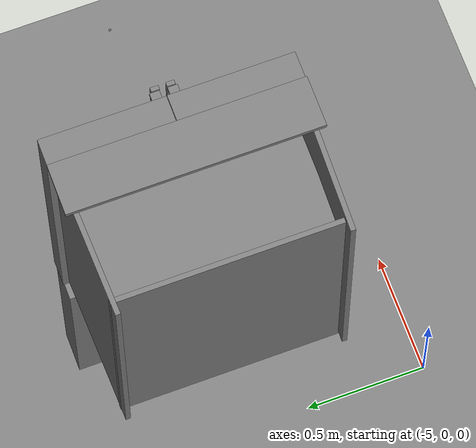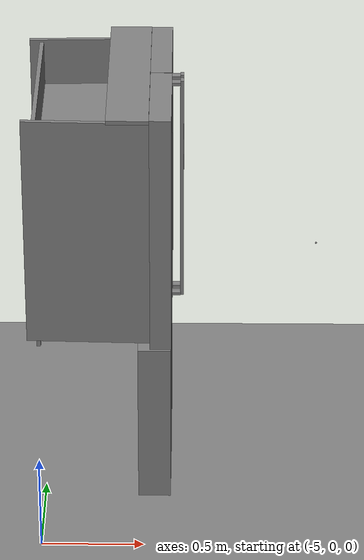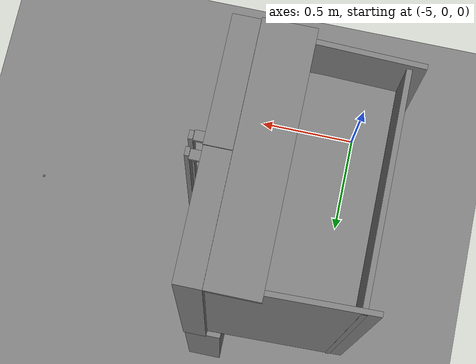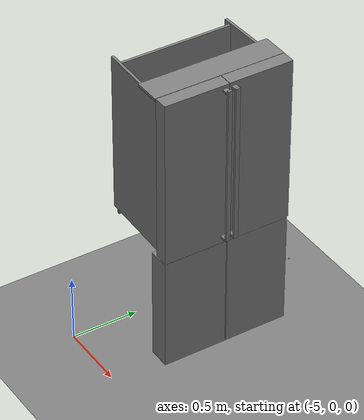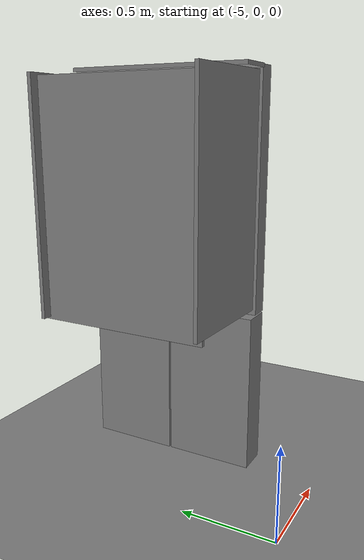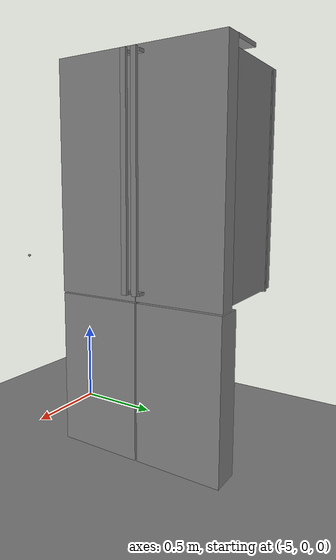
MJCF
<mujoco>
    <option gravity="0.000000000 0.000000000 -9.810000420" timestep="0.0049999999" integrator="implicitfast" density="1.225" viscosity="1.8000001e-05" noslip_iterations="10" iterations="100" sdf_iterations="50">
        <flag multiccd="disable"/>
    </option>
    <size memory="1000M"/>
    <compiler coordinate="local"/>
    <worldbody>
        <light cutoff="30" pos="0 1 1" dir="0 -1 -2"/>
        <light cutoff="30" pos="0 -1 1" dir="0 1 -2"/>
        <body pos="-4.455995083 0.348160446 1.533870339" euler="0.000000000 0.000000000 0.000000000" name="openloong_gripper_2f85_fix_base_usda_fridge_left_up">
            <geom contype="1" conaffinity="1" density="1000" type="box" material="" rgba="0.500000000 0.500000000 0.500000000 1.000000000" solimp="0.899999976 0.949999988 0.001000000" friction="1.000000000 0.005000000 0.000100000" solref="0.020000000 1.000000000" margin="0" condim="3" group="0" pos="0.034918308 0.246351242 -0.000000358" quat="1.000000000 0.000000000 0.000000000 0.000013381" size="0.052000001 0.243000001 0.625000000" name="openloong_gripper_2f85_fix_base_usda_Fridge_02_a_1E34127E_D39F_43C1_AADC_7FA39F014B09"/>
            <geom contype="1" conaffinity="1" density="1000" type="box" material="" rgba="0.500000000 0.500000000 0.500000000 1.000000000" solimp="0.899999976 0.949999988 0.001000000" friction="1.000000000 0.005000000 0.000100000" solref="0.020000000 1.000000000" margin="0" condim="3" group="0" pos="-0.055340290 0.240164995 -0.197626591" quat="0.999999940 0.000000000 0.000000000 0.000271916" size="0.035000000 0.200000003 0.075999998" name="openloong_gripper_2f85_fix_base_usda_Fridge_02_g_2AE08570_6054_46A7_8A8A_26EE40069DBD"/>
            <geom contype="1" conaffinity="1" density="1000" type="box" material="" rgba="0.500000000 0.500000000 0.500000000 1.000000000" solimp="0.899999976 0.949999988 0.001000000" friction="1.000000000 0.005000000 0.000100000" solref="0.020000000 1.000000000" margin="0" condim="3" group="0" pos="-0.036716461 0.240169704 0.099823833" quat="1.000000000 0.000000000 0.000000000 0.000120342" size="0.020000000 0.200000003 0.070000000" name="openloong_gripper_2f85_fix_base_usda_Fridge_02_f_44908C3E_CD45_4C89_99BC_1EF87E12AAF5"/>
            <geom contype="1" conaffinity="1" density="1000" type="box" material="" rgba="0.500000000 0.500000000 0.500000000 1.000000000" solimp="0.899999976 0.949999988 0.001000000" friction="1.000000000 0.005000000 0.000100000" solref="0.020000000 1.000000000" margin="0" condim="3" group="0" pos="0.133846283 0.458910882 0.011316895" quat="1.000000000 0.000000000 0.000000000 0.000000417" size="0.008500000 0.016000001 0.595000029" name="openloong_gripper_2f85_fix_base_usda_Fridge_02_b_AE86C1A9_909D_48AA_9ACF_E3A81EE5582D"/>
            <geom contype="1" conaffinity="1" density="1000" type="box" material="" rgba="0.500000000 0.500000000 0.500000000 1.000000000" solimp="0.899999976 0.949999988 0.001000000" friction="1.000000000 0.005000000 0.000100000" solref="0.020000000 1.000000000" margin="0" condim="3" group="0" pos="-0.036197186 0.240169704 0.373237491" quat="1.000000000 0.000000000 0.000000000 0.000087470" size="0.020000000 0.200000003 0.070000000" name="openloong_gripper_2f85_fix_base_usda_Fridge_02_e_599AA16B_876D_4E3B_88F2_DA8EC415063E"/>
            <geom contype="1" conaffinity="1" density="1000" type="box" material="" rgba="0.500000000 0.500000000 0.500000000 1.000000000" solimp="0.899999976 0.949999988 0.001000000" friction="1.000000000 0.005000000 0.000100000" solref="0.020000000 1.000000000" margin="0" condim="3" group="0" pos="0.097751617 0.454878092 -0.576283276" quat="1.000000000 0.000000000 0.000000000 0.000000417" size="0.029999999 0.018999999 0.008000000" name="openloong_gripper_2f85_fix_base_usda_Fridge_02_c_48D5666B_61F7_4845_992C_57A23FD7D55E"/>
            <geom contype="1" conaffinity="1" density="1000" type="box" material="" rgba="0.500000000 0.500000000 0.500000000 1.000000000" solimp="0.899999976 0.949999988 0.001000000" friction="1.000000000 0.005000000 0.000100000" solref="0.020000000 1.000000000" margin="0" condim="3" group="0" pos="0.096112251 0.454878092 0.589555621" quat="1.000000000 0.000000000 0.000000000 0.000000417" size="0.029999999 0.018999999 0.008000000" name="openloong_gripper_2f85_fix_base_usda_Fridge_02_d_36351959_9598_4E1C_AB06_C87C0091A377"/>
            <joint armature="0" stiffness="0" damping="5" axis="0.000000 0.000000 -1.000000" limited="true" range="0.000000000 180.000000000" type="hinge" name="openloong_gripper_2f85_fix_base_usda_fridge_left_up_joint"/>
        </body>
        <body pos="-4.456572533 1.328142047 1.533870339" euler="0.000000000 0.000000000 0.000000000" name="openloong_gripper_2f85_fix_base_usda_fridge_right_up">
            <geom contype="1" conaffinity="1" density="1000" type="box" material="" rgba="0.500000000 0.500000000 0.500000000 1.000000000" solimp="0.899999976 0.949999988 0.001000000" friction="1.000000000 0.005000000 0.000100000" solref="0.020000000 1.000000000" margin="0" condim="3" group="0" pos="-0.042358875 -0.244417667 0.003658533" quat="0.999999881 0.000000000 0.000000000 0.000160277" size="0.020000000 0.189999998 0.500000000" name="openloong_gripper_2f85_fix_base_usda_geom_88A46C4F_CD07_403A_83FD_CB5121D262A3"/>
            <geom contype="1" conaffinity="1" density="1000" type="box" material="" rgba="0.500000000 0.500000000 0.500000000 1.000000000" solimp="0.899999976 0.949999988 0.001000000" friction="1.000000000 0.005000000 0.000100000" solref="0.020000000 1.000000000" margin="0" condim="3" group="0" pos="0.134432793 -0.461116314 0.011315942" quat="0.999999940 0.000000075 -0.000000089 0.000017196" size="0.008500000 0.016000001 0.595000029" name="openloong_gripper_2f85_fix_base_usda_geom_6CDEE529_5345_48F4_9048_9B342C09A335"/>
            <geom contype="1" conaffinity="1" density="1000" type="box" material="" rgba="0.500000000 0.500000000 0.500000000 1.000000000" solimp="0.899999976 0.949999988 0.001000000" friction="1.000000000 0.005000000 0.000100000" solref="0.020000000 1.000000000" margin="0" condim="3" group="0" pos="0.096698761 -0.456393361 0.589552999" quat="0.999999881 0.000000074 -0.000000089 0.000032246" size="0.029999999 0.018999999 0.008000000" name="openloong_gripper_2f85_fix_base_usda_geom_464CC1FD_E386_41E4_AD23_4D7CAE8E3862"/>
            <geom contype="1" conaffinity="1" density="1000" type="box" material="" rgba="0.500000000 0.500000000 0.500000000 1.000000000" solimp="0.899999976 0.949999988 0.001000000" friction="1.000000000 0.005000000 0.000100000" solref="0.020000000 1.000000000" margin="0" condim="3" group="0" pos="0.098338127 -0.456895828 -0.576284051" quat="0.999999940 0.000000074 -0.000000089 0.000029832" size="0.029999999 0.018999999 0.008000000" name="openloong_gripper_2f85_fix_base_usda_geom_302EAB5B_4240_400C_A874_5386121E2270"/>
            <geom contype="1" conaffinity="1" density="1000" type="box" material="" rgba="0.500000000 0.500000000 0.500000000 1.000000000" solimp="0.899999976 0.949999988 0.001000000" friction="1.000000000 0.005000000 0.000100000" solref="0.020000000 1.000000000" margin="0" condim="3" group="0" pos="0.034286022 -0.245587349 0.000602603" quat="0.999999881 0.000000000 0.000000000 0.000051796" size="0.050999999 0.243000001 0.625000000" name="openloong_gripper_2f85_fix_base_usda_geom_4D175753_EC28_43EC_8FCE_C739A325C33B"/>
            <joint armature="0" stiffness="0" damping="5" axis="0.000000 0.000000 1.000000" limited="true" range="0.000000000 180.000000000" type="hinge" name="openloong_gripper_2f85_fix_base_usda_fridge_right_up_joint"/>
        </body>
        <body pos="0.000000000 0.000000000 0.000000000" euler="0.000000000 0.000000000 0.000000000" name="StaticObjcets_StaticObjcets">
            <geom contype="2" conaffinity="2" density="1000" type="box" material="" rgba="0.500000000 0.500000000 0.500000000 1.000000000" solimp="0.899999976 0.949999988 0.001000000" friction="1.000000000 0.005000000 0.000100000" solref="0.020000000 1.000000000" margin="0" condim="3" group="0" pos="-4.761908531 0.835612714 1.871172667" quat="1.000000000 0.000000000 0.000000000 0.000000000" size="0.250000000 0.439999998 0.005000000" name="StaticObjcets_geom_82CE28E5_3763_4A8E_945E_F900660B748A"/>
            <geom contype="2" conaffinity="2" density="1000" type="box" material="" rgba="0.500000000 0.500000000 0.500000000 1.000000000" solimp="0.899999976 0.949999988 0.001000000" friction="1.000000000 0.005000000 0.000100000" solref="0.020000000 1.000000000" margin="0" condim="3" group="0" pos="-4.769333839 0.386707336 1.535037637" quat="0.707029462 0.707027197 -0.010532650 -0.010532619" size="0.300000012 0.600000024 0.010000000" name="StaticObjcets_geom_C1793A29_C063_4D5A_B812_6AC841684D70"/>
            <geom contype="2" conaffinity="2" density="1000" type="box" material="" rgba="0.500000000 0.500000000 0.500000000 1.000000000" solimp="0.899999976 0.949999988 0.001000000" friction="1.000000000 0.005000000 0.000100000" solref="0.020000000 1.000000000" margin="0" condim="3" group="0" pos="-4.763467789 0.835180044 1.691508532" quat="1.000000000 0.000000000 0.000000000 0.000000000" size="0.250000000 0.439999998 0.005000000" name="StaticObjcets_geom_3E88D3F6_8D3B_4957_A9DB_9E96D35D41C7"/>
            <geom contype="2" conaffinity="2" density="1000" type="box" material="" rgba="0.500000000 0.500000000 0.500000000 1.000000000" solimp="0.899999976 0.949999988 0.001000000" friction="1.000000000 0.005000000 0.000100000" solref="0.020000000 1.000000000" margin="0" condim="3" group="0" pos="-4.454798698 1.079833508 0.470532238" quat="0.707107067 0.000000000 0.000000000 0.707106471" size="0.239999995 0.079999998 0.430000007" name="StaticObjcets_Fridge_03_CC1C1F27_27F1_459C_9B0E_C740018DF81D"/>
            <geom contype="1" conaffinity="1" density="1000" type="plane" material="" rgba="0.500000000 0.500000000 0.500000000 1.000000000" solimp="0.899999976 0.949999988 0.001000000" friction="1.000000000 0.005000000 0.000100000" solref="0.020000000 1.000000000" margin="0" condim="3" group="0" pos="-0.043989260 0.222946882 0.032030921" quat="1.000000000 0.000000000 0.000000000 0.000000000" size="8.000000000 8.000000000 1.000000000" name="StaticObjcets_geom_5016030B_515A_40A4_A623_E356E13D5B07"/>
            <geom contype="2" conaffinity="2" density="1000" type="box" material="" rgba="0.500000000 0.500000000 0.500000000 1.000000000" solimp="0.899999976 0.949999988 0.001000000" friction="1.000000000 0.005000000 0.000100000" solref="0.020000000 1.000000000" margin="0" condim="3" group="0" pos="-4.771282196 1.281533480 1.516736507" quat="0.707029462 0.707027197 0.010532652 0.010532617" size="0.300000012 0.600000024 0.010000000" name="StaticObjcets_geom_D74B35D0_369E_4F0C_95AE_F4F5CA13886A"/>
            <geom contype="2" conaffinity="2" density="1000" type="box" material="" rgba="0.500000000 0.500000000 0.500000000 1.000000000" solimp="0.899999976 0.949999988 0.001000000" friction="1.000000000 0.005000000 0.000100000" solref="0.020000000 1.000000000" margin="0" condim="3" group="0" pos="-4.765080929 0.836613894 1.500948071" quat="1.000000000 0.000000000 0.000000000 0.000000000" size="0.250000000 0.439999998 0.005000000" name="StaticObjcets_geom_FF306B66_7A38_4815_AC19_B505694E499E"/>
            <geom contype="2" conaffinity="2" density="1000" type="box" material="" rgba="0.500000000 0.500000000 0.500000000 1.000000000" solimp="0.899999976 0.949999988 0.001000000" friction="1.000000000 0.005000000 0.000100000" solref="0.020000000 1.000000000" margin="0" condim="3" group="0" pos="-4.717486858 0.835144579 1.096694350" quat="1.000000000 0.000000000 0.000000000 0.000000000" size="0.200000003 0.439999998 0.119999997" name="StaticObjcets_geom_579D9F4F_0CA8_4EE2_B648_3F0199911D08"/>
            <geom contype="2" conaffinity="2" density="1000" type="box" material="" rgba="0.500000000 0.500000000 0.500000000 1.000000000" solimp="0.899999976 0.949999988 0.001000000" friction="1.000000000 0.005000000 0.000100000" solref="0.020000000 1.000000000" margin="0" condim="3" group="0" pos="-4.453287601 0.590693057 0.470532209" quat="0.707107067 0.000000000 0.000000000 0.707106471" size="0.239999995 0.079999998 0.430000007" name="StaticObjcets_Fridge_04_a_36BCCB66_259C_4DE2_9777_AC67927262FD"/>
            <geom contype="1" conaffinity="1" density="1000" type="box" material="" rgba="0.500000000 0.500000000 0.500000000 1.000000000" solimp="0.899999976 0.949999988 0.001000000" friction="1.000000000 0.005000000 0.000100000" solref="0.020000000 1.000000000" margin="0" condim="3" group="0" pos="-4.573544502 0.835462213 2.151423454" quat="1.000000000 0.000000000 0.000000000 0.000000000" size="0.100000001 0.490000010 0.010000000" name="StaticObjcets_geom_2FAF0A1C_EBCD_4987_8396_DE60D09F446E"/>
            <geom contype="2" conaffinity="2" density="1000" type="box" material="" rgba="0.500000000 0.500000000 0.500000000 1.000000000" solimp="0.899999976 0.949999988 0.001000000" friction="1.000000000 0.005000000 0.000100000" solref="0.020000000 1.000000000" margin="0" condim="3" group="0" pos="-5.012205601 0.835292637 1.504703879" quat="0.500000417 0.499999970 0.499999970 0.499999553" size="0.449999988 0.600000024 0.010000000" name="StaticObjcets_Fridge_only_08_3CB88C81_698F_4273_B94E_6941ECCA1738"/>
        </body>
        <body pos="-3.662749529 0.835145235 0.026324987" euler="0.000000000 0.000000000 180.000000000" mocap="true" name="openloong_gripper_2f85_fix_base_usda_leftHandMocap"/>
        <body pos="-3.662749529 0.835145235 0.026324987" euler="0.000000000 0.000000000 180.000000000" mocap="true" name="openloong_gripper_2f85_fix_base_usda_rightHandMocap"/>
        <body pos="-3.662749529 0.835145235 1.226325035" euler="0.000000000 0.000000000 180.000000000" name="openloong_gripper_2f85_fix_base_usda_base_link">
            <geom contype="1" conaffinity="1" density="1000" type="mesh" material="" rgba="0.783999979 0.783999979 0.783999979 1.000000000" solimp="0.899999976 0.949999988 0.001000000" friction="1.000000000 0.005000000 0.000100000" solref="0.020000000 1.000000000" margin="0" condim="3" group="3" mesh="base_link" pos="0.000000000 0.000000000 0.000000000" quat="1.000000000 0.000000000 0.000000000 0.000000000" size="1.000000000 1.000000000 1.000000000" name="openloong_gripper_2f85_fix_base_usda__geom_7_44CFB93D_E2D2_4723_A8C8_4D6CCFAC6C28"/>
            <site size="0.005000000 0.005000000 0.005000000" rgba="0.500000000 0.500000000 0.500000000 1.000000000" pos="0.000000000 0.000000000 0.000000000" quat="1.000000000 0.000000000 0.000000000 0.000000000" group="0" type="sphere" name="openloong_gripper_2f85_fix_base_usda_imu"/>
            <inertial mass="22.447001" pos="-0.005664100 -0.001336700 0.238289997" diaginertia="0.374352545 0.277180195 0.220617250" quat="0.999247074 0.035235517 -0.015086859 0.006023135"/>
            <body pos="0.000000000 0.000000000 0.299999952" euler="0.000000000 0.000000000 0.000000000" name="openloong_gripper_2f85_fix_base_usda_dummy_body">
                <geom contype="1" conaffinity="1" density="1000" type="sphere" material="" rgba="0.783999979 0.783999979 0.783999979 1.000000000" solimp="0.899999976 0.949999988 0.001000000" friction="1.000000000 0.005000000 0.000100000" solref="0.020000000 1.000000000" margin="0" condim="3" group="3" pos="0.000000000 0.000000000 0.000000000" quat="1.000000000 0.000000000 0.000000000 0.000000000" size="0.010000000 0.000000000 0.000000000" name="openloong_gripper_2f85_fix_base_usda__geom_8_AA5C10C9_0110_4296_9B9D_AF2E2FD33649"/>
                <joint armature="0.0099999998" stiffness="0" damping="0.1" axis="0.000000 0.000000 1.000000" type="hinge" name="openloong_gripper_2f85_fix_base_usda_dummy_joint"/>
                <site size="0.010000000 0.005000000 0.005000000" rgba="0.500000000 0.500000000 0.500000000 1.000000000" pos="0.000000000 0.000000000 0.000000000" quat="1.000000000 0.000000000 0.000000000 0.000000000" group="3" type="sphere" name="openloong_gripper_2f85_fix_base_usda_dummy_site"/>
            </body>
            <body pos="0.009000063 0.000000000 0.406399965" euler="0.000000000 0.000000000 0.000000000" name="openloong_gripper_2f85_fix_base_usda_Link_head_yaw">
                <geom contype="1" conaffinity="1" density="1000" type="mesh" material="" rgba="0.783999979 0.783999979 0.783999979 1.000000000" solimp="0.899999976 0.949999988 0.001000000" friction="1.000000000 0.005000000 0.000100000" solref="0.020000000 1.000000000" margin="0" condim="3" group="3" mesh="Link_head_yaw" pos="0.000000000 0.000000000 0.000000000" quat="1.000000000 0.000000000 0.000000000 0.000000000" size="1.000000000 1.000000000 1.000000000" name="openloong_gripper_2f85_fix_base_usda__geom_10_DA440A39_70E5_4F09_AD6D_29F34AE4E614"/>
                <inertial mass="0.84249002" pos="0.000000000 -0.002081400 0.044801001" diaginertia="0.000700588 0.000629000 0.000553812" quat="0.706933022 -0.015675601 0.015677100 0.706933022"/>
                <body pos="0.000000000 -0.034600019 0.048500061" euler="0.000000000 0.000000000 0.000000000" name="openloong_gripper_2f85_fix_base_usda_Link_head_pitch">
                    <geom contype="1" conaffinity="1" density="1000" type="mesh" material="" rgba="0.783999979 0.783999979 0.783999979 1.000000000" solimp="0.899999976 0.949999988 0.001000000" friction="1.000000000 0.005000000 0.000100000" solref="0.020000000 1.000000000" margin="0" condim="3" group="3" mesh="Link_head_pitch" pos="0.000000000 0.000000000 0.000000000" quat="1.000000000 0.000000000 0.000000000 0.000000000" size="1.000000000 1.000000000 1.000000000" name="openloong_gripper_2f85_fix_base_usda__geom_12_54C10716_C574_45FD_9EE9_A9815A56265C"/>
                    <inertial mass="1.3943" pos="0.020569000 0.033004001 0.125000000" diaginertia="0.006381400 0.006289940 0.004481460" quat="0.973390222 0.008406822 0.228157058 0.019624906"/>
                    <body pos="0.000000000 0.029999971 0.000000000" euler="0.000000000 0.000000000 0.000000000" name="openloong_gripper_2f85_fix_base_usda_neck_center_body">
                        <site size="0.010000000 0.005000000 0.005000000" rgba="0.500000000 0.500000000 0.500000000 1.000000000" pos="0.000000000 0.000000000 0.000000000" quat="1.000000000 0.000000000 0.000000000 0.000000000" group="3" type="sphere" name="openloong_gripper_2f85_fix_base_usda_neck_center_site"/>
                        <body pos="0.019999981 0.000000000 0.149999976" euler="-0.000002229 39.998176575 -90.000205994" name="openloong_gripper_2f85_fix_base_usda_camera_head">
                            <site size="0.010000000 0.005000000 0.005000000" rgba="0.500000000 0.500000000 0.500000000 1.000000000" pos="0.000000000 0.000000000 0.000000000" quat="1.000000000 0.000000000 0.000000000 0.000000000" group="3" type="sphere" name="openloong_gripper_2f85_fix_base_usda_camera_head_site"/>
                        </body>
                    </body>
                </body>
            </body>
            <body pos="0.003999949 -0.161599994 0.392199993" euler="0.000000000 0.000000000 0.000000000" name="openloong_gripper_2f85_fix_base_usda_Link_arm_r_01">
                <geom contype="1" conaffinity="1" density="1000" type="mesh" material="" rgba="0.783999979 0.783999979 0.783999979 1.000000000" solimp="0.899999976 0.949999988 0.001000000" friction="1.000000000 0.005000000 0.000100000" solref="0.020000000 1.000000000" margin="0" condim="3" group="3" mesh="Link_arm_r_01" pos="0.000000000 0.000000000 0.000000000" quat="1.000000000 0.000000000 0.000000000 0.000000000" size="1.000000000 1.000000000 1.000000000" name="openloong_gripper_2f85_fix_base_usda__geom_14_6FBB4032_7167_41EB_92A3_BB1AF4E439B0"/>
                <joint armature="0.0099999998" stiffness="0" damping="1" axis="0.000000 -1.000000 0.000000" limited="true" range="-170.000015259 170.000015259" type="hinge" name="openloong_gripper_2f85_fix_base_usda_J_arm_r_01"/>
                <inertial mass="0.75641" pos="0.004494600 -0.038293999 -0.000001874" diaginertia="0.000842990 0.000803050 0.000587120" quat="-0.000163502 0.707098067 0.000812463 0.707115054"/>
                <body pos="-0.042000055 -0.041000009 0.000000000" euler="0.000000000 0.000000000 0.000000000" name="openloong_gripper_2f85_fix_base_usda_Link_arm_r_02">
                    <geom contype="1" conaffinity="1" density="1000" type="mesh" material="" rgba="0.783999979 0.783999979 0.783999979 1.000000000" solimp="0.899999976 0.949999988 0.001000000" friction="1.000000000 0.005000000 0.000100000" solref="0.020000000 1.000000000" margin="0" condim="3" group="3" mesh="Link_arm_r_02" pos="0.000000000 0.000000000 0.000000000" quat="1.000000000 0.000000000 0.000000000 0.000000000" size="1.000000000 1.000000000 1.000000000" name="openloong_gripper_2f85_fix_base_usda__geom_16_0BC9E5D3_C265_4B7B_8426_AF65AFE2D7B8"/>
                    <joint armature="0.0099999998" stiffness="0" damping="1" axis="-1.000000 0.000000 0.000000" limited="true" range="-105.000244141 105.000244141" type="hinge" name="openloong_gripper_2f85_fix_base_usda_J_arm_r_02"/>
                    <inertial mass="0.98500001" pos="0.041999999 -0.067430697 0.000000000" diaginertia="0.002262690 0.001730990 0.001154020" quat="0.500000000 0.500000000 -0.500000000 0.500000000"/>
                    <body pos="0.042000055 -0.122599959 0.000000000" euler="0.000000000 0.000000000 0.000000000" name="openloong_gripper_2f85_fix_base_usda_Link_arm_r_03">
                        <geom contype="1" conaffinity="1" density="1000" type="mesh" material="" rgba="0.783999979 0.783999979 0.783999979 1.000000000" solimp="0.899999976 0.949999988 0.001000000" friction="1.000000000 0.005000000 0.000100000" solref="0.020000000 1.000000000" margin="0" condim="3" group="3" mesh="Link_arm_r_03" pos="0.000000000 0.000000000 0.000000000" quat="1.000000000 0.000000000 0.000000000 0.000000000" size="1.000000000 1.000000000 1.000000000" name="openloong_gripper_2f85_fix_base_usda__geom_18_7CAA0E4F_6892_44A8_8C98_58F40CEFDEE0"/>
                        <joint armature="0.0099999998" stiffness="0" damping="1" axis="0.000000 -1.000000 0.000000" limited="true" range="-170.000015259 170.000015259" type="hinge" name="openloong_gripper_2f85_fix_base_usda_J_arm_r_03"/>
                        <inertial mass="0.95899999" pos="-0.001413580 -0.164663002 0.020757901" diaginertia="0.002101340 0.002064590 0.000754802" quat="0.560480952 0.454391927 -0.443732947 0.531497955"/>
                        <body pos="0.035300016 -0.177399993 0.024000049" euler="0.000000000 0.000000000 0.000000000" name="openloong_gripper_2f85_fix_base_usda_Link_arm_r_04">
                            <geom contype="1" conaffinity="1" density="1000" type="mesh" material="" rgba="0.783999979 0.783999979 0.783999979 1.000000000" solimp="0.899999976 0.949999988 0.001000000" friction="1.000000000 0.005000000 0.000100000" solref="0.020000000 1.000000000" margin="0" condim="3" group="3" mesh="Link_arm_r_04" pos="0.000000000 0.000000000 0.000000000" quat="1.000000000 0.000000000 0.000000000 0.000000000" size="1.000000000 1.000000000 1.000000000" name="openloong_gripper_2f85_fix_base_usda__geom_20_90D56D47_7773_4429_AD8A_5089248B1315"/>
                            <joint armature="0.0099999998" stiffness="0" damping="1" axis="-1.000000 0.000000 0.000000" limited="true" range="0.000000000 170.000015259" type="hinge" name="openloong_gripper_2f85_fix_base_usda_J_arm_r_04"/>
                            <inertial mass="0.60000002" pos="-0.038727000 -0.060766999 -0.021003000" diaginertia="0.001092610 0.000712422 0.000645102" quat="0.327701002 0.632602990 -0.467366993 0.523443997"/>
                            <body pos="-0.035300016 -0.103500009 -0.024000049" euler="0.000000000 0.000000000 0.000000000" name="openloong_gripper_2f85_fix_base_usda_Link_arm_r_05">
                                <geom contype="1" conaffinity="1" density="1000" type="mesh" material="" rgba="0.783999979 0.783999979 0.783999979 1.000000000" solimp="0.899999976 0.949999988 0.001000000" friction="1.000000000 0.005000000 0.000100000" solref="0.020000000 1.000000000" margin="0" condim="3" group="3" mesh="Link_arm_r_05" pos="0.000000000 0.000000000 0.000000000" quat="1.000000000 0.000000000 0.000000000 0.000000000" size="1.000000000 1.000000000 1.000000000" name="openloong_gripper_2f85_fix_base_usda__geom_22_48DA8BBA_90A9_434A_B728_C2EE904F7DA5"/>
                                <joint armature="0.0099999998" stiffness="0" damping="1" axis="0.000000 -1.000000 0.000000" limited="true" range="-170.000015259 170.000015259" type="hinge" name="openloong_gripper_2f85_fix_base_usda_J_arm_r_05"/>
                                <inertial mass="0.68976003" pos="0.000032712 -0.068658002 -0.000111780" diaginertia="0.002522510 0.002411100 0.000448695" quat="0.707660973 0.706543028 -0.002603360 0.002470550"/>
                                <body pos="-0.026499987 -0.196499944 0.000000000" euler="0.000000000 0.000000000 0.000000000" name="openloong_gripper_2f85_fix_base_usda_Link_arm_r_06">
                                    <geom contype="1" conaffinity="1" density="1000" type="mesh" material="" rgba="0.783999979 0.783999979 0.783999979 1.000000000" solimp="0.899999976 0.949999988 0.001000000" friction="1.000000000 0.005000000 0.000100000" solref="0.020000000 1.000000000" margin="0" condim="3" group="3" mesh="Link_arm_r_06" pos="0.000000000 0.000000000 0.000000000" quat="1.000000000 0.000000000 0.000000000 0.000000000" size="1.000000000 1.000000000 1.000000000" name="openloong_gripper_2f85_fix_base_usda__geom_24_0BED5ECF_A322_4788_B9C0_22E2F265C4EB"/>
                                    <joint armature="0.0099999998" stiffness="0" damping="1" axis="1.000000 0.000000 0.000000" limited="true" range="-105.000244141 105.000244141" type="hinge" name="openloong_gripper_2f85_fix_base_usda_J_arm_r_06"/>
                                    <inertial mass="0.28" pos="0.026078001 -0.000000896 0.001663700" diaginertia="0.000156930 0.000145601 0.000104979" quat="0.707080841 0.001851080 0.001883810 0.707127810"/>
                                    <body pos="0.026499987 0.000000000 0.031800032" euler="0.000000000 0.000000000 0.000000000" name="openloong_gripper_2f85_fix_base_usda_Link_arm_r_07">
                                        <geom contype="1" conaffinity="1" density="1000" type="mesh" material="" rgba="0.783999979 0.783999979 0.783999979 1.000000000" solimp="0.899999976 0.949999988 0.001000000" friction="1.000000000 0.005000000 0.000100000" solref="0.020000000 1.000000000" margin="0" condim="3" group="3" mesh="Link_arm_r_07" pos="0.000000000 0.000000000 0.000000000" quat="1.000000000 0.000000000 0.000000000 0.000000000" size="1.000000000 1.000000000 1.000000000" name="openloong_gripper_2f85_fix_base_usda__geom_26_94416155_E16D_4FB8_8124_4E834B71FFE2"/>
                                        <joint armature="0.0099999998" stiffness="0" damping="1" axis="0.000000 0.000000 1.000000" limited="true" range="-60.000133514 60.000133514" type="hinge" name="openloong_gripper_2f85_fix_base_usda_J_arm_r_07"/>
                                        <inertial mass="0.61353999" pos="-0.007859000 -0.158170000 -0.027736001" diaginertia="0.003037610 0.002570910 0.000729379" quat="0.427542925 0.443532884 -0.553093910 0.560867906"/>
                                        <body pos="0.000000000 0.286999941 -0.269999981" euler="150.000350952 0.000000000 0.000000000" name="openloong_gripper_2f85_fix_base_usda_camera_wrist_r">
                                            <site size="0.010000000 0.005000000 0.005000000" rgba="0.500000000 0.500000000 0.500000000 1.000000000" pos="0.000000000 0.000000000 0.000000000" quat="1.000000000 0.000000000 0.000000000 0.000000000" group="3" type="sphere" name="openloong_gripper_2f85_fix_base_usda_camera_wrist_r_site"/>
                                        </body>
                                        <body pos="0.000000000 -0.220000029 -0.032999992" euler="0.000000000 0.000000000 179.999969482" name="openloong_gripper_2f85_fix_base_usda_ee_center_body_r">
                                            <site size="0.010000000 0.005000000 0.005000000" rgba="0.500000000 0.500000000 0.500000000 1.000000000" pos="0.000000000 0.000000000 0.000000000" quat="1.000000000 0.000000000 0.000000000 0.000000000" group="3" type="sphere" name="openloong_gripper_2f85_fix_base_usda_ee_center_site_r"/>
                                        </body>
                                        <body pos="0.000000000 -0.065999985 -0.031000018" euler="89.999984741 0.000000000 180.000000000" name="openloong_gripper_2f85_fix_base_usda_zbr_base_link">
                                            <geom contype="1" conaffinity="1" density="1000" type="mesh" material="" rgba="0.783999979 0.783999979 0.783999979 1.000000000" solimp="0.899999976 0.949999988 0.001000000" friction="1.000000000 0.005000000 0.000100000" solref="0.020000000 1.000000000" margin="0" condim="3" group="3" mesh="base" pos="0.000000000 0.000000000 0.000000000" quat="1.000000000 0.000000000 0.000000000 0.000000000" size="1.000000238 1.000000238 1.000000238" name="openloong_gripper_2f85_fix_base_usda__geom_30_11F18BF1_4462_41A0_908D_88EC7AB7BEBF"/>
                                            <inertial mass="0.77744102" pos="0.000000000 -0.000027039 0.035467502" diaginertia="0.000260285 0.000225381 0.000152708" quat="0.999998808 -0.001528488 0.000000000 0.000000000"/>
                                            <body pos="-0.030601032 0.004750133 0.065704480" euler="-89.999977112 0.000000000 0.000000000" name="openloong_gripper_2f85_fix_base_usda_r_left_driver">
                                                <geom contype="1" conaffinity="1" density="1000" type="mesh" material="" rgba="0.783999979 0.783999979 0.783999979 1.000000000" solimp="0.899999976 0.949999988 0.001000000" friction="1.000000000 0.005000000 0.000100000" solref="0.020000000 1.000000000" margin="0" condim="3" group="3" mesh="driver" pos="0.030601032 0.054904357 -0.004699946" quat="0.707106709 0.707106590 0.000000000 0.000000000" size="1.000000238 1.000000238 1.000000238" name="openloong_gripper_2f85_fix_base_usda__geom_32_34B040B4_2DC0_4BEC_A4A7_070F508944A9"/>
                                                <joint armature="0.0049999999" stiffness="0" damping="0.1" axis="0.000000 0.000000 1.000000" limited="true" range="0.000000000 51.566200256" type="hinge" name="openloong_gripper_2f85_fix_base_usda_r_left_driver_joint"/>
                                                <inertial mass="0.0089956298" pos="0.000000000 0.017754700 0.001073140" diaginertia="0.000001724 0.000001609 0.000000322" quat="0.681301236 0.732003212 0.000000000 0.000000000"/>
                                                <body pos="-0.031425007 0.004532219 -0.010200026" euler="0.000000000 0.000000000 180.000000000" name="openloong_gripper_2f85_fix_base_usda_r_left_coupler">
                                                    <geom contype="1" conaffinity="1" density="1000" type="mesh" material="" rgba="0.783999979 0.783999979 0.783999979 1.000000000" solimp="0.899999976 0.949999988 0.001000000" friction="1.000000000 0.005000000 0.000100000" solref="0.020000000 1.000000000" margin="0" condim="3" group="3" mesh="coupler" pos="-0.062026039 -0.050372254 0.005499960" quat="0.707106709 -0.707106590 0.000000000 0.000000000" size="1.000000238 1.000000238 1.000000238" name="openloong_gripper_2f85_fix_base_usda__geom_34_F1468899_394D_4965_ABE3_A2AA82A54922"/>
                                                    <inertial mass="0.0140974" pos="0.000000000 0.003012090 0.023217499" diaginertia="0.000004162 0.000003522 0.000000888" quat="0.705635548 -0.045590367 0.045590367 0.705635548"/>
                                                </body>
                                            </body>
                                            <body pos="-0.012700084 -0.011999848 0.072219983" euler="-89.999977112 0.000000000 0.000000000" name="openloong_gripper_2f85_fix_base_usda_r_left_spring_link">
                                                <geom contype="1" conaffinity="1" density="1000" type="mesh" material="" rgba="0.783999979 0.783999979 0.783999979 1.000000000" solimp="0.899999976 0.949999988 0.001000000" friction="1.000000000 0.005000000 0.000100000" solref="0.020000000 1.000000000" margin="0" condim="3" group="3" mesh="spring_link" pos="0.012700084 0.061419860 0.012050035" quat="0.707106709 0.707106590 0.000000000 0.000000000" size="1.000000238 1.000000238 1.000000238" name="openloong_gripper_2f85_fix_base_usda__geom_36_5AF0BD81_2038_49D5_A77C_F379E0FD7829"/>
                                                <joint armature="0.001" stiffness="0.050000001" damping="0.00125" axis="0.000000 0.000000 1.000000" limited="true" range="-17.000000000 51.566200256" type="hinge" name="openloong_gripper_2f85_fix_base_usda_r_left_spring_link_joint"/>
                                                <inertial mass="0.0221642" pos="-0.000000009 0.018162400 0.021265799" diaginertia="0.000008969 0.000006717 0.000002639" quat="0.663403213 -0.244737089 0.244737089 0.663403213"/>
                                                <body pos="-0.038208015 -0.042500269 0.002950073" euler="180.000000000 0.000000000 -0.002179886" name="openloong_gripper_2f85_fix_base_usda_r_left_follower">
                                                    <geom contype="1" conaffinity="1" density="1000" type="mesh" material="" rgba="0.783999979 0.783999979 0.783999979 1.000000000" solimp="0.899999976 0.949999988 0.001000000" friction="1.000000000 0.005000000 0.000100000" solref="0.020000000 1.000000000" margin="0" condim="3" group="3" mesh="follower" pos="0.050907861 -0.103919886 -0.009099962" quat="0.707106709 -0.707106590 0.000000000 -0.000000000" size="1.000000238 1.000000238 1.000000238" name="openloong_gripper_2f85_fix_base_usda__geom_39_89D21EB3_9D3D_4DF7_BA33_A6602BF0BDD3"/>
                                                    <geom contype="1" conaffinity="1" density="1000" type="mesh" material="" rgba="0.783999979 0.783999979 0.783999979 1.000000000" solimp="0.899999976 0.949999988 0.001000000" friction="1.000000000 0.005000000 0.000100000" solref="0.020000000 1.000000000" margin="0" condim="3" group="3" mesh="tongue" pos="0.050907861 -0.103919886 -0.009099962" quat="0.707106709 -0.707106590 0.000000000 -0.000000000" size="1.000000238 1.000000238 1.000000238" name="openloong_gripper_2f85_fix_base_usda__geom_40_B409E03A_FFC6_4463_8DBE_B47A628C81B2"/>
                                                    <joint armature="0.001" stiffness="0" damping="0.1" axis="0.000000 0.000000 1.000000" limited="true" range="-49.999961853 51.566200256" type="hinge" name="openloong_gripper_2f85_fix_base_usda_r_left_follower"/>
                                                    <inertial mass="0.0125222" pos="0.000000000 -0.011046000 0.012478600" diaginertia="0.000002674 0.000002456 0.000000602" quat="0.986436546 0.164143041 0.000000000 0.000000000"/>
                                                    <body pos="-0.037789829 -0.103916071 -0.009099962" euler="-89.999961853 0.000000000 -0.000000000" name="openloong_gripper_2f85_fix_base_usda_r_left_pad">
                                                        <geom contype="1" conaffinity="1" density="1000" type="box" material="" rgba="0.550000012 0.550000012 0.550000012 1.000000000" solimp="0.949999988 0.990000010 0.001000000" friction="0.699999988 0.005000000 0.000100000" solref="0.020000000 1.000000000" margin="0" condim="3" group="3" mass="1e-06" pos="0.043257486 -0.000000119 0.119999796" quat="0.999999821 0.000000000 0.000000000 0.000000000" size="0.002000001 0.011000003 0.009375002" name="openloong_gripper_2f85_fix_base_usda_r_left_pad1_A4C693A4_87D7_477C_A7BF_78779E5EC1E1"/>
                                                        <geom contype="1" conaffinity="1" density="1000" type="box" material="" rgba="0.449999988 0.449999988 0.449999988 1.000000000" solimp="0.949999988 0.990000010 0.001000000" friction="0.600000024 0.005000000 0.000100000" solref="0.020000000 1.000000000" margin="0" condim="3" group="3" mass="1e-06" pos="0.043257724 -0.000000119 0.138749987" quat="0.999999821 0.000000000 0.000000000 0.000000000" size="0.002000001 0.011000003 0.009375002" name="openloong_gripper_2f85_fix_base_usda_r_left_pad2_6D7C7BBD_F3D4_47B6_B238_A4EA40CE0E7C"/>
                                                    </body>
                                                </body>
                                            </body>
                                            <body pos="0.030601032 -0.004749895 0.065704480" euler="89.999984741 0.000000000 180.000000000" name="openloong_gripper_2f85_fix_base_usda_r_right_driver">
                                                <geom contype="1" conaffinity="1" density="1000" type="mesh" material="" rgba="0.783999979 0.783999979 0.783999979 1.000000000" solimp="0.899999976 0.949999988 0.001000000" friction="1.000000000 0.005000000 0.000100000" solref="0.020000000 1.000000000" margin="0" condim="3" group="3" mesh="driver" pos="0.030601032 0.054904357 -0.004699946" quat="0.707106829 0.707106709 0.000000000 0.000000000" size="1.000000238 1.000000238 1.000000238" name="openloong_gripper_2f85_fix_base_usda__geom_42_5CDF6B74_A6B9_4430_8995_56C3B789CE99"/>
                                                <joint armature="0.0049999999" stiffness="0" damping="0.1" axis="0.000000 0.000000 1.000000" limited="true" range="0.000000000 51.566200256" type="hinge" name="openloong_gripper_2f85_fix_base_usda_r_right_driver_joint"/>
                                                <inertial mass="0.0089956298" pos="0.000000000 0.017754700 0.001073140" diaginertia="0.000001724 0.000001609 0.000000322" quat="0.681301236 0.732003212 0.000000000 0.000000000"/>
                                                <body pos="-0.031425007 0.004532219 -0.010200026" euler="0.000000000 0.000000000 180.000000000" name="openloong_gripper_2f85_fix_base_usda_r_right_coupler">
                                                    <geom contype="1" conaffinity="1" density="1000" type="mesh" material="" rgba="0.783999979 0.783999979 0.783999979 1.000000000" solimp="0.899999976 0.949999988 0.001000000" friction="1.000000000 0.005000000 0.000100000" solref="0.020000000 1.000000000" margin="0" condim="3" group="3" mesh="coupler" pos="-0.062026039 -0.050372254 0.005499960" quat="0.707106829 -0.707106709 0.000000000 0.000000000" size="1.000000238 1.000000238 1.000000238" name="openloong_gripper_2f85_fix_base_usda__geom_44_B50C334A_4ACA_4377_8E63_70BEB67FE49C"/>
                                                    <inertial mass="0.0140974" pos="0.000000000 0.003012090 0.023217499" diaginertia="0.000004162 0.000003522 0.000000888" quat="0.705635548 -0.045590367 0.045590367 0.705635548"/>
                                                </body>
                                            </body>
                                            <body pos="0.012700084 0.012000087 0.072219983" euler="89.999984741 0.000000000 180.000000000" name="openloong_gripper_2f85_fix_base_usda_r_right_spring_link">
                                                <geom contype="1" conaffinity="1" density="1000" type="mesh" material="" rgba="0.783999979 0.783999979 0.783999979 1.000000000" solimp="0.899999976 0.949999988 0.001000000" friction="1.000000000 0.005000000 0.000100000" solref="0.020000000 1.000000000" margin="0" condim="3" group="3" mesh="spring_link" pos="0.012700084 0.061419860 0.012050035" quat="0.707106829 0.707106709 0.000000000 0.000000000" size="1.000000238 1.000000238 1.000000238" name="openloong_gripper_2f85_fix_base_usda__geom_46_40A776B5_6348_4203_9A43_09D4F4B2C3FA"/>
                                                <joint armature="0.001" stiffness="0.050000001" damping="0.00125" axis="0.000000 0.000000 1.000000" limited="true" range="-17.000000000 51.566200256" type="hinge" name="openloong_gripper_2f85_fix_base_usda_r_right_spring_link_joint"/>
                                                <inertial mass="0.0221642" pos="-0.000000009 0.018162400 0.021265799" diaginertia="0.000008969 0.000006717 0.000002639" quat="0.663403213 -0.244737089 0.244737089 0.663403213"/>
                                                <body pos="-0.038208015 -0.042500269 0.002949954" euler="180.000000000 0.000000000 0.000000000" name="openloong_gripper_2f85_fix_base_usda_r_right_follower">
                                                    <geom contype="1" conaffinity="1" density="1000" type="mesh" material="" rgba="0.783999979 0.783999979 0.783999979 1.000000000" solimp="0.899999976 0.949999988 0.001000000" friction="1.000000000 0.005000000 0.000100000" solref="0.020000000 1.000000000" margin="0" condim="3" group="3" mesh="tongue" pos="0.050907861 -0.103919886 -0.009099962" quat="0.707106829 -0.707106709 0.000000000 0.000000000" size="1.000000238 1.000000238 1.000000238" name="openloong_gripper_2f85_fix_base_usda__geom_49_F4DBF1A4_A24C_4F46_B1DF_6885A2E0ABE3"/>
                                                    <geom contype="1" conaffinity="1" density="1000" type="mesh" material="" rgba="0.783999979 0.783999979 0.783999979 1.000000000" solimp="0.899999976 0.949999988 0.001000000" friction="1.000000000 0.005000000 0.000100000" solref="0.020000000 1.000000000" margin="0" condim="3" group="3" mesh="follower" pos="0.050907861 -0.103919886 -0.009099962" quat="0.707106829 -0.707106709 0.000000000 0.000000000" size="1.000000238 1.000000238 1.000000238" name="openloong_gripper_2f85_fix_base_usda__geom_50_EA6E069F_879E_4113_BFFD_B5F153398F49"/>
                                                    <joint armature="0.001" stiffness="0" damping="0.1" axis="0.000000 0.000000 1.000000" limited="true" range="-49.999961853 51.566200256" type="hinge" name="openloong_gripper_2f85_fix_base_usda_r_right_follower_joint"/>
                                                    <inertial mass="0.0125222" pos="0.000000000 -0.011046000 0.012478600" diaginertia="0.000002674 0.000002456 0.000000602" quat="0.986436546 0.164143041 0.000000000 0.000000000"/>
                                                    <body pos="-0.037789829 -0.103915952 -0.009099962" euler="-89.999984741 0.000000000 0.000000000" name="openloong_gripper_2f85_fix_base_usda_r_right_pad">
                                                        <geom contype="1" conaffinity="1" density="1000" type="box" material="" rgba="0.550000012 0.550000012 0.550000012 1.000000000" solimp="0.949999988 0.990000010 0.001000000" friction="0.699999988 0.005000000 0.000100000" solref="0.020000000 1.000000000" margin="0" condim="3" group="3" mass="1e-06" pos="0.043257963 0.000000000 0.119999677" quat="1.000000000 0.000000000 0.000000000 0.000000000" size="0.002000001 0.011000003 0.009375002" name="openloong_gripper_2f85_fix_base_usda_r_right_pad1_0CE24C3E_F73C_489B_8F9D_38D79A2BECB9"/>
                                                        <geom contype="1" conaffinity="1" density="1000" type="box" material="" rgba="0.449999988 0.449999988 0.449999988 1.000000000" solimp="0.949999988 0.990000010 0.001000000" friction="0.600000024 0.005000000 0.000100000" solref="0.020000000 1.000000000" margin="0" condim="3" group="3" mass="1e-06" pos="0.043257963 0.000000119 0.138750106" quat="1.000000000 0.000000000 0.000000000 0.000000000" size="0.002000001 0.011000003 0.009375002" name="openloong_gripper_2f85_fix_base_usda_r_right_pad2_61E91020_998E_4707_9964_D9563A93B5AD"/>
                                                    </body>
                                                </body>
                                            </body>
                                        </body>
                                    </body>
                                </body>
                            </body>
                        </body>
                    </body>
                </body>
            </body>
            <body pos="0.003999949 0.161599994 0.392199993" euler="0.000000000 0.000000000 0.000000000" name="openloong_gripper_2f85_fix_base_usda_Link_arm_l_01">
                <geom contype="1" conaffinity="1" density="1000" type="mesh" material="" rgba="0.783999979 0.783999979 0.783999979 1.000000000" solimp="0.899999976 0.949999988 0.001000000" friction="1.000000000 0.005000000 0.000100000" solref="0.020000000 1.000000000" margin="0" condim="3" group="3" mesh="Link_arm_l_01" pos="0.000000000 0.000000000 0.000000000" quat="1.000000000 0.000000000 0.000000000 0.000000000" size="1.000000000 1.000000000 1.000000000" name="openloong_gripper_2f85_fix_base_usda__geom_52_6502451B_B49D_4CF4_A322_23A3C182B3B7"/>
                <joint armature="0.0099999998" stiffness="0" damping="1" axis="0.000000 1.000000 0.000000" limited="true" range="-170.000015259 170.000015259" type="hinge" name="openloong_gripper_2f85_fix_base_usda_J_arm_l_01"/>
                <inertial mass="0.75640601" pos="-0.004494650 0.038294200 -0.000001874" diaginertia="0.000842986 0.000803053 0.000587115" quat="-0.000812496 0.707115054 0.000163424 0.707098067"/>
                <body pos="0.042000055 0.041000009 0.000000000" euler="0.000000000 0.000000000 0.000000000" name="openloong_gripper_2f85_fix_base_usda_Link_arm_l_02">
                    <geom contype="1" conaffinity="1" density="1000" type="mesh" material="" rgba="0.783999979 0.783999979 0.783999979 1.000000000" solimp="0.899999976 0.949999988 0.001000000" friction="1.000000000 0.005000000 0.000100000" solref="0.020000000 1.000000000" margin="0" condim="3" group="3" mesh="Link_arm_l_02" pos="0.000000000 0.000000000 0.000000000" quat="1.000000000 0.000000000 0.000000000 0.000000000" size="1.000000000 1.000000000 1.000000000" name="openloong_gripper_2f85_fix_base_usda__geom_54_71BCAD6C_05F1_4802_A41F_AB3834A74A03"/>
                    <joint armature="0.0099999998" stiffness="0" damping="1" axis="-1.000000 0.000000 0.000000" limited="true" range="-105.000244141 105.000244141" type="hinge" name="openloong_gripper_2f85_fix_base_usda_J_arm_l_02"/>
                    <inertial mass="0.98500001" pos="-0.041999999 0.067430697 0.000000000" diaginertia="0.002262690 0.001730990 0.001154020" quat="0.500000000 0.500000000 -0.500000000 0.500000000"/>
                    <body pos="-0.042000055 0.122600019 0.000000000" euler="0.000000000 0.000000000 0.000000000" name="openloong_gripper_2f85_fix_base_usda_Link_arm_l_03">
                        <geom contype="1" conaffinity="1" density="1000" type="mesh" material="" rgba="0.783999979 0.783999979 0.783999979 1.000000000" solimp="0.899999976 0.949999988 0.001000000" friction="1.000000000 0.005000000 0.000100000" solref="0.020000000 1.000000000" margin="0" condim="3" group="3" mesh="Link_arm_l_03" pos="0.000000000 0.000000000 0.000000000" quat="1.000000000 0.000000000 0.000000000 0.000000000" size="1.000000000 1.000000000 1.000000000" name="openloong_gripper_2f85_fix_base_usda__geom_56_19A20B27_C913_4AF2_A8C7_53D71BA9EC96"/>
                        <joint armature="0.0099999998" stiffness="0" damping="1" axis="0.000000 1.000000 0.000000" limited="true" range="-170.000015259 170.000015259" type="hinge" name="openloong_gripper_2f85_fix_base_usda_J_arm_l_03"/>
                        <inertial mass="0.95899999" pos="0.001413580 0.164663002 0.020757901" diaginertia="0.002101340 0.002064590 0.000754802" quat="0.443732947 0.531497955 -0.560480952 0.454391927"/>
                        <body pos="-0.035300016 0.177399993 0.024000049" euler="0.000000000 0.000000000 0.000000000" name="openloong_gripper_2f85_fix_base_usda_Link_arm_l_04">
                            <geom contype="1" conaffinity="1" density="1000" type="mesh" material="" rgba="0.783999979 0.783999979 0.783999979 1.000000000" solimp="0.899999976 0.949999988 0.001000000" friction="1.000000000 0.005000000 0.000100000" solref="0.020000000 1.000000000" margin="0" condim="3" group="3" mesh="Link_arm_l_04" pos="0.000000000 0.000000000 0.000000000" quat="1.000000000 0.000000000 0.000000000 0.000000000" size="1.000000000 1.000000000 1.000000000" name="openloong_gripper_2f85_fix_base_usda__geom_58_B4E29364_C1EB_411A_AE2C_63242A52774A"/>
                            <joint armature="0.0099999998" stiffness="0" damping="1" axis="1.000000 0.000000 0.000000" limited="true" range="0.000000000 170.000015259" type="hinge" name="openloong_gripper_2f85_fix_base_usda_J_arm_l_04"/>
                            <inertial mass="0.60000002" pos="0.038727000 0.060767200 -0.021003200" diaginertia="0.001092570 0.000712419 0.000645098" quat="0.467370987 0.523440003 -0.327692002 0.632607996"/>
                            <body pos="0.035300016 0.103500009 -0.024000049" euler="0.000000000 0.000000000 0.000000000" name="openloong_gripper_2f85_fix_base_usda_Link_arm_l_05">
                                <geom contype="1" conaffinity="1" density="1000" type="mesh" material="" rgba="0.783999979 0.783999979 0.783999979 1.000000000" solimp="0.899999976 0.949999988 0.001000000" friction="1.000000000 0.005000000 0.000100000" solref="0.020000000 1.000000000" margin="0" condim="3" group="3" mesh="Link_arm_l_05" pos="0.000000000 0.000000000 0.000000000" quat="1.000000000 0.000000000 0.000000000 0.000000000" size="1.000000000 1.000000000 1.000000000" name="openloong_gripper_2f85_fix_base_usda__geom_60_105EA4C0_E82F_4CB1_B36D_FCB4607DAB96"/>
                                <joint armature="0.0099999998" stiffness="0" damping="1" axis="0.000000 1.000000 0.000000" limited="true" range="-170.000015259 170.000015259" type="hinge" name="openloong_gripper_2f85_fix_base_usda_J_arm_l_05"/>
                                <inertial mass="0.68976003" pos="-0.000032712 0.068658002 -0.000111780" diaginertia="0.002522510 0.002411100 0.000448695" quat="0.706543028 0.707660973 0.002470550 -0.002603360"/>
                                <body pos="0.026499987 0.196500003 0.000000000" euler="0.000000000 0.000000000 0.000000000" name="openloong_gripper_2f85_fix_base_usda_Link_arm_l_06">
                                    <geom contype="1" conaffinity="1" density="1000" type="mesh" material="" rgba="0.783999979 0.783999979 0.783999979 1.000000000" solimp="0.899999976 0.949999988 0.001000000" friction="1.000000000 0.005000000 0.000100000" solref="0.020000000 1.000000000" margin="0" condim="3" group="3" mesh="Link_arm_l_06" pos="0.000000000 0.000000000 0.000000000" quat="1.000000000 0.000000000 0.000000000 0.000000000" size="1.000000000 1.000000000 1.000000000" name="openloong_gripper_2f85_fix_base_usda__geom_62_2CBDF291_4D75_4A6C_8924_AA8829DB3690"/>
                                    <joint armature="0.0099999998" stiffness="0" damping="1" axis="-1.000000 0.000000 0.000000" limited="true" range="-105.000244141 105.000244141" type="hinge" name="openloong_gripper_2f85_fix_base_usda_J_arm_l_06"/>
                                    <inertial mass="0.28" pos="-0.026077701 0.000000896 0.001663730" diaginertia="0.000156927 0.000145598 0.000104981" quat="0.707080841 -0.001851280 -0.001884020 0.707127810"/>
                                    <body pos="-0.026499987 0.000000000 0.031800032" euler="0.000000000 0.000000000 0.000000000" name="openloong_gripper_2f85_fix_base_usda_Link_arm_l_07">
                                        <geom contype="1" conaffinity="1" density="1000" type="mesh" material="" rgba="0.783999979 0.783999979 0.783999979 1.000000000" solimp="0.899999976 0.949999988 0.001000000" friction="1.000000000 0.005000000 0.000100000" solref="0.020000000 1.000000000" margin="0" condim="3" group="3" mesh="Link_arm_l_07" pos="0.000000000 0.000000000 0.000000000" quat="1.000000000 0.000000000 0.000000000 0.000000000" size="1.000000000 1.000000000 1.000000000" name="openloong_gripper_2f85_fix_base_usda__geom_64_F2CD9B36_713F_4A42_9A03_2A4BC8EED022"/>
                                        <joint armature="0.0099999998" stiffness="0" damping="1" axis="0.000000 0.000000 1.000000" limited="true" range="-60.000133514 60.000133514" type="hinge" name="openloong_gripper_2f85_fix_base_usda_J_arm_l_07"/>
                                        <inertial mass="0.61353999" pos="-0.007787200 0.157049999 -0.027733000" diaginertia="0.003037200 0.002570420 0.000729374" quat="0.443562120 0.427539080 -0.560871124 0.553070128"/>
                                        <body pos="0.000000000 -0.287000000 -0.269999981" euler="-150.000350952 -0.000000001 179.976669312" name="openloong_gripper_2f85_fix_base_usda_camera_wrist_l">
                                            <site size="0.010000000 0.005000000 0.005000000" rgba="0.500000000 0.500000000 0.500000000 1.000000000" pos="0.000000000 0.000000000 0.000000000" quat="1.000000000 0.000000000 0.000000000 0.000000000" group="3" type="sphere" name="openloong_gripper_2f85_fix_base_usda_camera_wrist_l_site"/>
                                        </body>
                                        <body pos="0.000000000 0.219999999 -0.032999992" euler="0.000000000 0.000000000 0.000000000" name="openloong_gripper_2f85_fix_base_usda_ee_center_body">
                                            <site size="0.010000000 0.005000000 0.005000000" rgba="0.500000000 0.500000000 0.500000000 1.000000000" pos="0.000000000 0.000000000 0.000000000" quat="1.000000000 0.000000000 0.000000000 0.000000000" group="3" type="sphere" name="openloong_gripper_2f85_fix_base_usda_ee_center_site"/>
                                        </body>
                                        <body pos="0.000000000 0.066000000 -0.031000018" euler="-90.000007629 0.000000000 0.000000000" name="openloong_gripper_2f85_fix_base_usda_zbll_base_link">
                                            <geom contype="1" conaffinity="1" density="1000" type="mesh" material="" rgba="0.783999979 0.783999979 0.783999979 1.000000000" solimp="0.899999976 0.949999988 0.001000000" friction="1.000000000 0.005000000 0.000100000" solref="0.020000000 1.000000000" margin="0" condim="3" group="3" mesh="base" pos="0.000000000 0.000000000 0.000000000" quat="1.000000000 0.000000000 0.000000000 0.000000000" size="1.000000000 1.000000000 1.000000000" name="openloong_gripper_2f85_fix_base_usda__geom_68_FD581A78_1708_48E1_93E0_D51320B5B93D"/>
                                            <inertial mass="0.77744102" pos="0.000000000 -0.000027039 0.035467502" diaginertia="0.000260285 0.000225381 0.000152708" quat="0.999998808 -0.001528488 0.000000000 0.000000000"/>
                                            <body pos="-0.030601025 0.004750252 0.065704346" euler="-89.999992371 0.000000000 0.000000000" name="openloong_gripper_2f85_fix_base_usda_l_left_driver">
                                                <geom contype="1" conaffinity="1" density="1000" type="mesh" material="" rgba="0.783999979 0.783999979 0.783999979 1.000000000" solimp="0.899999976 0.949999988 0.001000000" friction="1.000000000 0.005000000 0.000100000" solref="0.020000000 1.000000000" margin="0" condim="3" group="3" mesh="driver" pos="0.030601025 0.054904491 -0.004699945" quat="0.707106829 0.707106709 0.000000000 0.000000000" size="1.000000000 1.000000000 1.000000000" name="openloong_gripper_2f85_fix_base_usda__geom_70_37666279_703E_4994_99FF_998945C377F7"/>
                                                <joint armature="0.0049999999" stiffness="0" damping="0.1" axis="0.000000 0.000000 1.000000" limited="true" range="0.000000000 51.566200256" type="hinge" name="openloong_gripper_2f85_fix_base_usda_l_left_driver_joint"/>
                                                <inertial mass="0.0089956298" pos="0.000000000 0.017754700 0.001073140" diaginertia="0.000001724 0.000001609 0.000000322" quat="0.681301236 0.732003212 0.000000000 0.000000000"/>
                                                <body pos="-0.031424999 0.004532233 -0.010200024" euler="0.000000000 0.000000000 180.000000000" name="openloong_gripper_2f85_fix_base_usda_l_left_coupler">
                                                    <geom contype="1" conaffinity="1" density="1000" type="mesh" material="" rgba="0.783999979 0.783999979 0.783999979 1.000000000" solimp="0.899999976 0.949999988 0.001000000" friction="1.000000000 0.005000000 0.000100000" solref="0.020000000 1.000000000" margin="0" condim="3" group="3" mesh="coupler" pos="-0.062026024 -0.050372299 0.005499959" quat="0.707106829 -0.707106709 0.000000000 0.000000000" size="1.000000000 1.000000000 1.000000000" name="openloong_gripper_2f85_fix_base_usda__geom_72_B87F7CA7_10D0_424B_B026_C0AFBAA5A580"/>
                                                    <inertial mass="0.0140974" pos="0.000000000 0.003012090 0.023217499" diaginertia="0.000004162 0.000003522 0.000000888" quat="0.705635548 -0.045590367 0.045590367 0.705635548"/>
                                                </body>
                                            </body>
                                            <body pos="-0.012700081 -0.011999846 0.072219968" euler="-89.999992371 0.000000000 0.000000000" name="openloong_gripper_2f85_fix_base_usda_l_left_spring_link">
                                                <geom contype="1" conaffinity="1" density="1000" type="mesh" material="" rgba="0.783999979 0.783999979 0.783999979 1.000000000" solimp="0.899999976 0.949999988 0.001000000" friction="1.000000000 0.005000000 0.000100000" solref="0.020000000 1.000000000" margin="0" condim="3" group="3" mesh="spring_link" pos="0.012700081 0.061420009 0.012050033" quat="0.707106829 0.707106709 0.000000000 0.000000000" size="1.000000000 1.000000000 1.000000000" name="openloong_gripper_2f85_fix_base_usda__geom_74_C21F67F7_BF88_41FF_9BCE_6199D66CE272"/>
                                                <joint armature="0.001" stiffness="0.050000001" damping="0.00125" axis="0.000000 0.000000 1.000000" limited="true" range="-17.000000000 51.566200256" type="hinge" name="openloong_gripper_2f85_fix_base_usda_l_left_spring_link_joint"/>
                                                <inertial mass="0.0221642" pos="-0.000000009 0.018162400 0.021265799" diaginertia="0.000008969 0.000006717 0.000002639" quat="0.663403213 -0.244737089 0.244737089 0.663403213"/>
                                                <body pos="-0.038208008 -0.042500287 0.002949953" euler="180.000000000 0.000000000 -0.002179887" name="openloong_gripper_2f85_fix_base_usda_l_left_follower">
                                                    <geom contype="1" conaffinity="1" density="1000" type="mesh" material="" rgba="0.783999979 0.783999979 0.783999979 1.000000000" solimp="0.899999976 0.949999988 0.001000000" friction="1.000000000 0.005000000 0.000100000" solref="0.020000000 1.000000000" margin="0" condim="3" group="3" mesh="follower" pos="0.050908089 -0.103920005 -0.009099960" quat="0.707106829 -0.707106709 0.000000000 -0.000000000" size="1.000000000 1.000000000 1.000000000" name="openloong_gripper_2f85_fix_base_usda__geom_77_4AA2784F_324B_43F7_9CFD_326E22C87734"/>
                                                    <geom contype="1" conaffinity="1" density="1000" type="mesh" material="" rgba="0.783999979 0.783999979 0.783999979 1.000000000" solimp="0.899999976 0.949999988 0.001000000" friction="1.000000000 0.005000000 0.000100000" solref="0.020000000 1.000000000" margin="0" condim="3" group="3" mesh="tongue" pos="0.050908089 -0.103920005 -0.009099960" quat="0.707106829 -0.707106709 0.000000000 -0.000000000" size="1.000000000 1.000000000 1.000000000" name="openloong_gripper_2f85_fix_base_usda__geom_78_DD9CB5E0_9D4A_4767_B62F_9ABAA0D0D560"/>
                                                    <joint armature="0.001" stiffness="0" damping="0.1" axis="0.000000 0.000000 1.000000" limited="true" range="-49.999961853 51.566200256" type="hinge" name="openloong_gripper_2f85_fix_base_usda_l_left_follower"/>
                                                    <inertial mass="0.0125222" pos="0.000000000 -0.011046000 0.012478600" diaginertia="0.000002674 0.000002456 0.000000602" quat="0.986436546 0.164143041 0.000000000 0.000000000"/>
                                                    <body pos="-0.037789583 -0.103916004 -0.009099960" euler="-89.999984741 0.000000000 -0.000000000" name="openloong_gripper_2f85_fix_base_usda_l_left_pad">
                                                        <geom contype="1" conaffinity="1" density="1000" type="box" material="" rgba="0.449999988 0.449999988 0.449999988 1.000000000" solimp="0.949999988 0.990000010 0.001000000" friction="0.600000024 0.005000000 0.000100000" solref="0.020000000 1.000000000" margin="0" condim="3" group="3" mass="1e-06" pos="0.043257952 0.000000000 0.138750181" quat="1.000000000 0.000000000 0.000000000 0.000000000" size="0.002000000 0.011000000 0.009375000" name="openloong_gripper_2f85_fix_base_usda_l_left_pad2_9910FFC2_226C_41A8_8D7A_AA828E86C64C"/>
                                                        <geom contype="1" conaffinity="1" density="1000" type="box" material="" rgba="0.550000012 0.550000012 0.550000012 1.000000000" solimp="0.949999988 0.990000010 0.001000000" friction="0.699999988 0.005000000 0.000100000" solref="0.020000000 1.000000000" margin="0" condim="3" group="3" mass="1e-06" pos="0.043257952 0.000000000 0.119999990" quat="1.000000000 0.000000000 0.000000000 0.000000000" size="0.002000000 0.011000000 0.009375000" name="openloong_gripper_2f85_fix_base_usda_l_left_pad1_9979C894_CA7E_4AE9_AC3C_7A28842DE343"/>
                                                    </body>
                                                </body>
                                            </body>
                                            <body pos="0.030601025 -0.004749894 0.065704346" euler="89.999992371 0.000000000 180.000000000" name="openloong_gripper_2f85_fix_base_usda_l_right_driver">
                                                <geom contype="1" conaffinity="1" density="1000" type="mesh" material="" rgba="0.783999979 0.783999979 0.783999979 1.000000000" solimp="0.899999976 0.949999988 0.001000000" friction="1.000000000 0.005000000 0.000100000" solref="0.020000000 1.000000000" margin="0" condim="3" group="3" mesh="driver" pos="0.030601025 0.054904498 -0.004699945" quat="0.707106829 0.707106709 0.000000000 0.000000000" size="1.000000000 1.000000000 1.000000000" name="openloong_gripper_2f85_fix_base_usda__geom_80_2CFF03E2_1E2B_4441_9029_917A0217E54D"/>
                                                <joint armature="0.0049999999" stiffness="0" damping="0.1" axis="0.000000 0.000000 1.000000" limited="true" range="0.000000000 51.566200256" type="hinge" name="openloong_gripper_2f85_fix_base_usda_l_right_driver_joint"/>
                                                <inertial mass="0.0089956298" pos="0.000000000 0.017754700 0.001073140" diaginertia="0.000001724 0.000001609 0.000000322" quat="0.681301236 0.732003212 0.000000000 0.000000000"/>
                                                <body pos="-0.031424999 0.004532233 -0.010200024" euler="0.000000000 0.000000000 180.000000000" name="openloong_gripper_2f85_fix_base_usda_l_right_coupler">
                                                    <geom contype="1" conaffinity="1" density="1000" type="mesh" material="" rgba="0.783999979 0.783999979 0.783999979 1.000000000" solimp="0.899999976 0.949999988 0.001000000" friction="1.000000000 0.005000000 0.000100000" solref="0.020000000 1.000000000" margin="0" condim="3" group="3" mesh="coupler" pos="-0.062026024 -0.050372299 0.005499959" quat="0.707106829 -0.707106709 0.000000000 0.000000000" size="1.000000000 1.000000000 1.000000000" name="openloong_gripper_2f85_fix_base_usda__geom_82_D190FEB1_3F85_4D95_9877_74B68FF3268D"/>
                                                    <inertial mass="0.0140974" pos="0.000000000 0.003012090 0.023217499" diaginertia="0.000004162 0.000003522 0.000000888" quat="0.705635548 -0.045590367 0.045590367 0.705635548"/>
                                                </body>
                                            </body>
                                            <body pos="0.012700081 0.012000084 0.072219968" euler="89.999992371 0.000000000 180.000000000" name="openloong_gripper_2f85_fix_base_usda_l_right_spring_link">
                                                <geom contype="1" conaffinity="1" density="1000" type="mesh" material="" rgba="0.783999979 0.783999979 0.783999979 1.000000000" solimp="0.899999976 0.949999988 0.001000000" friction="1.000000000 0.005000000 0.000100000" solref="0.020000000 1.000000000" margin="0" condim="3" group="3" mesh="spring_link" pos="0.012700081 0.061420005 0.012050033" quat="0.707106829 0.707106709 0.000000000 0.000000000" size="1.000000000 1.000000000 1.000000000" name="openloong_gripper_2f85_fix_base_usda__geom_84_9F718360_E208_4ED9_B0A7_376ED2BFDB29"/>
                                                <joint armature="0.001" stiffness="0.050000001" damping="0.00125" axis="0.000000 0.000000 1.000000" limited="true" range="-17.000000000 51.566200256" type="hinge" name="openloong_gripper_2f85_fix_base_usda_l_right_spring_link_joint"/>
                                                <inertial mass="0.0221642" pos="-0.000000009 0.018162400 0.021265799" diaginertia="0.000008969 0.000006717 0.000002639" quat="0.663403213 -0.244737089 0.244737089 0.663403213"/>
                                                <body pos="-0.038208008 -0.042500295 0.002949953" euler="180.000000000 0.000000000 0.000000000" name="openloong_gripper_2f85_fix_base_usda_l_right_follower">
                                                    <geom contype="1" conaffinity="1" density="1000" type="mesh" material="" rgba="0.783999979 0.783999979 0.783999979 1.000000000" solimp="0.899999976 0.949999988 0.001000000" friction="1.000000000 0.005000000 0.000100000" solref="0.020000000 1.000000000" margin="0" condim="3" group="3" mesh="tongue" pos="0.050907850 -0.103919998 -0.009100080" quat="0.707106829 -0.707106709 0.000000000 0.000000000" size="1.000000000 1.000000000 1.000000000" name="openloong_gripper_2f85_fix_base_usda__geom_87_6BAD57B5_A2CD_4EF3_BFB6_5C7FA39EC5CA"/>
                                                    <geom contype="1" conaffinity="1" density="1000" type="mesh" material="" rgba="0.783999979 0.783999979 0.783999979 1.000000000" solimp="0.899999976 0.949999988 0.001000000" friction="1.000000000 0.005000000 0.000100000" solref="0.020000000 1.000000000" margin="0" condim="3" group="3" mesh="follower" pos="0.050907850 -0.103919998 -0.009100080" quat="0.707106829 -0.707106709 0.000000000 0.000000000" size="1.000000000 1.000000000 1.000000000" name="openloong_gripper_2f85_fix_base_usda__geom_88_9820765C_D6E8_4658_B579_9BC57249FED5"/>
                                                    <joint armature="0.001" stiffness="0" damping="0.1" axis="0.000000 0.000000 1.000000" limited="true" range="-49.999961853 51.566200256" type="hinge" name="openloong_gripper_2f85_fix_base_usda_l_right_follower_joint"/>
                                                    <inertial mass="0.0125222" pos="0.000000000 -0.011046000 0.012478600" diaginertia="0.000002674 0.000002456 0.000000602" quat="0.986436546 0.164143041 0.000000000 0.000000000"/>
                                                    <body pos="-0.037789583 -0.103915997 -0.009100080" euler="-89.999984741 0.000000000 0.000000000" name="openloong_gripper_2f85_fix_base_usda_l_right_pad">
                                                        <geom contype="1" conaffinity="1" density="1000" type="box" material="" rgba="0.449999988 0.449999988 0.449999988 1.000000000" solimp="0.949999988 0.990000010 0.001000000" friction="0.600000024 0.005000000 0.000100000" solref="0.020000000 1.000000000" margin="0" condim="3" group="3" mass="1e-06" pos="0.043257952 0.000000119 0.138749987" quat="1.000000000 0.000000000 0.000000000 0.000000000" size="0.002000000 0.011000000 0.009375000" name="openloong_gripper_2f85_fix_base_usda_l_right_pad2_37F08880_EB8E_4BAA_BAB9_6169E3092ADF"/>
                                                        <geom contype="1" conaffinity="1" density="1000" type="box" material="" rgba="0.550000012 0.550000012 0.550000012 1.000000000" solimp="0.949999988 0.990000010 0.001000000" friction="0.699999988 0.005000000 0.000100000" solref="0.020000000 1.000000000" margin="0" condim="3" group="3" mass="1e-06" pos="0.043257952 0.000000000 0.119999975" quat="1.000000000 0.000000000 0.000000000 0.000000000" size="0.002000000 0.011000000 0.009375000" name="openloong_gripper_2f85_fix_base_usda_l_right_pad1_1FC4E121_9F3A_4060_BA0E_579670FFB59F"/>
                                                    </body>
                                                </body>
                                            </body>
                                        </body>
                                    </body>
                                </body>
                            </body>
                        </body>
                    </body>
                </body>
            </body>
            <body pos="0.000000000 -0.065249979 0.000000000" euler="0.000000000 0.000000000 0.000000000" name="openloong_gripper_2f85_fix_base_usda_Link_waist_pitch">
                <geom contype="1" conaffinity="1" density="1000" type="mesh" material="" rgba="0.783999979 0.783999979 0.783999979 1.000000000" solimp="0.899999976 0.949999988 0.001000000" friction="1.000000000 0.005000000 0.000100000" solref="0.020000000 1.000000000" margin="0" condim="3" group="3" mesh="Link_waist_pitch" pos="0.000000000 0.000000000 0.000000000" quat="1.000000000 0.000000000 0.000000000 0.000000000" size="1.000000000 1.000000000 1.000000000" name="openloong_gripper_2f85_fix_base_usda__geom_90_EAED480E_3211_4322_A5AD_D4F04204F256"/>
                <inertial mass="2.6963999" pos="-0.000734960 0.049924999 -0.000029695" diaginertia="0.006190620 0.005201250 0.004737120" quat="0.524125040 0.474713057 -0.522095084 0.476820052"/>
                <body pos="-0.063999891 0.065500021 0.000000000" euler="0.000000000 0.000000000 0.000000000" name="openloong_gripper_2f85_fix_base_usda_Link_waist_roll">
                    <geom contype="1" conaffinity="1" density="1000" type="mesh" material="" rgba="0.783999979 0.783999979 0.783999979 1.000000000" solimp="0.899999976 0.949999988 0.001000000" friction="1.000000000 0.005000000 0.000100000" solref="0.020000000 1.000000000" margin="0" condim="3" group="3" mesh="Link_waist_roll" pos="0.000000000 0.000000000 0.000000000" quat="1.000000000 0.000000000 0.000000000 0.000000000" size="1.000000000 1.000000000 1.000000000" name="openloong_gripper_2f85_fix_base_usda__geom_92_56C8F5FD_2439_4D6E_AC01_5C9C0F7E6D67"/>
                    <inertial mass="2.9806001" pos="-0.003742400 -0.001000000 -0.016856000" diaginertia="0.018825000 0.017314700 0.005873970" quat="0.576995134 0.408750087 0.408750087 0.576995134"/>
                    <body pos="0.067500114 0.000000000 -0.098000050" euler="0.000000000 0.000000000 0.000000000" name="openloong_gripper_2f85_fix_base_usda_Link_waist_yaw">
                        <geom contype="1" conaffinity="1" density="1000" type="mesh" material="" rgba="0.783999979 0.783999979 0.783999979 1.000000000" solimp="0.899999976 0.949999988 0.001000000" friction="1.000000000 0.005000000 0.000100000" solref="0.020000000 1.000000000" margin="0" condim="3" group="3" mesh="Link_waist_yaw" pos="0.000000000 0.000000000 0.000000000" quat="1.000000000 0.000000000 0.000000000 0.000000000" size="1.000000000 1.000000000 1.000000000" name="openloong_gripper_2f85_fix_base_usda__geom_94_9EF69344_5561_44DB_95EF_B2B2D2C5B489"/>
                        <inertial mass="7.3587999" pos="-0.096171997 -0.001000000 -0.057836000" diaginertia="0.109522998 0.089752100 0.032765999" quat="0.571972013 0.571972013 -0.415749997 0.415749997"/>
                        <body pos="-0.087500095 -0.120000005 -0.069000006" euler="0.000000000 0.000000000 0.000000000" name="openloong_gripper_2f85_fix_base_usda_Link_hip_r_roll">
                            <geom contype="1" conaffinity="1" density="1000" type="mesh" material="" rgba="0.783999979 0.783999979 0.783999979 1.000000000" solimp="0.899999976 0.949999988 0.001000000" friction="1.000000000 0.005000000 0.000100000" solref="0.020000000 1.000000000" margin="0" condim="3" group="3" mesh="Link_hip_r_roll" pos="0.000000000 0.000000000 0.000000000" quat="1.000000000 0.000000000 0.000000000 0.000000000" size="1.000000000 1.000000000 1.000000000" name="openloong_gripper_2f85_fix_base_usda__geom_96_54293947_FE03_4933_ADF3_1DE65682D230"/>
                            <inertial mass="2.4333999" pos="0.075724997 -0.001061600 0.016590999" diaginertia="0.004506770 0.003996270 0.003606060" quat="0.357336968 0.610613942 0.606069922 0.363510966"/>
                            <body pos="0.082250118 -0.000999987 -0.009999990" euler="0.000000000 0.000000000 0.000000000" name="openloong_gripper_2f85_fix_base_usda_Link_hip_r_yaw">
                                <geom contype="1" conaffinity="1" density="1000" type="mesh" material="" rgba="0.783999979 0.783999979 0.783999979 1.000000000" solimp="0.899999976 0.949999988 0.001000000" friction="1.000000000 0.005000000 0.000100000" solref="0.020000000 1.000000000" margin="0" condim="3" group="3" mesh="Link_hip_r_yaw" pos="0.000000000 0.000000000 0.000000000" quat="1.000000000 0.000000000 0.000000000 0.000000000" size="1.000000000 1.000000000 1.000000000" name="openloong_gripper_2f85_fix_base_usda__geom_98_E2B38970_3881_4E04_A354_B7ECBBA4FC74"/>
                                <inertial mass="3.4303" pos="-0.000000031 -0.007135600 -0.100630000" diaginertia="0.008090100 0.007736500 0.006631600" quat="0.706536055 0.028403703 -0.028403703 0.706536055"/>
                                <body pos="0.000000000 0.036750019 -0.105499983" euler="0.000000000 0.000000000 0.000000000" name="openloong_gripper_2f85_fix_base_usda_Link_hip_r_pitch">
                                    <geom contype="1" conaffinity="1" density="1000" type="mesh" material="" rgba="0.783999979 0.783999979 0.783999979 1.000000000" solimp="0.899999976 0.949999988 0.001000000" friction="1.000000000 0.005000000 0.000100000" solref="0.020000000 1.000000000" margin="0" condim="3" group="3" mesh="Link_hip_r_pitch" pos="0.000000000 0.000000000 0.000000000" quat="1.000000000 0.000000000 0.000000000 0.000000000" size="1.000000000 1.000000000 1.000000000" name="openloong_gripper_2f85_fix_base_usda__geom_100_CEFCDCBF_FC41_4835_8C2B_BE04F09B189B"/>
                                    <inertial mass="5.2378001" pos="0.001085600 -0.054970000 -0.145349994" diaginertia="0.043490201 0.037812300 0.015138500" quat="0.999495864 -0.015916798 0.013696698 0.023812896"/>
                                    <body pos="0.000000000 -0.011250019 -0.399999976" euler="0.000000000 0.000000000 0.000000000" name="openloong_gripper_2f85_fix_base_usda_Link_knee_r_pitch">
                                        <geom contype="1" conaffinity="1" density="1000" type="mesh" material="" rgba="0.783999979 0.783999979 0.783999979 1.000000000" solimp="0.899999976 0.949999988 0.001000000" friction="1.000000000 0.005000000 0.000100000" solref="0.020000000 1.000000000" margin="0" condim="3" group="3" mesh="Link_knee_r_pitch" pos="0.000000000 0.000000000 0.000000000" quat="1.000000000 0.000000000 0.000000000 0.000000000" size="1.000000000 1.000000000 1.000000000" name="openloong_gripper_2f85_fix_base_usda__geom_102_04B8104D_4213_4FBB_8103_90A91F94C108"/>
                                        <inertial mass="2.9775" pos="-0.009642500 0.000002934 -0.136010006" diaginertia="0.024215899 0.023851801 0.002284610" quat="0.782037616 -0.003061678 0.016178992 0.623013675"/>
                                        <body pos="0.000000000 0.000000000 -0.386999995" euler="0.000000000 0.000000000 0.000000000" name="openloong_gripper_2f85_fix_base_usda_Link_ankle_r_pitch">
                                            <geom contype="1" conaffinity="1" density="1000" type="mesh" material="" rgba="0.783999979 0.783999979 0.783999979 1.000000000" solimp="0.899999976 0.949999988 0.001000000" friction="1.000000000 0.005000000 0.000100000" solref="0.020000000 1.000000000" margin="0" condim="3" group="3" mesh="Link_ankle_r_pitch" pos="0.000000000 0.000000000 0.000000000" quat="1.000000000 0.000000000 0.000000000 0.000000000" size="1.000000000 1.000000000 1.000000000" name="openloong_gripper_2f85_fix_base_usda__geom_104_3611A596_34D4_4587_8365_EF08A9F29B81"/>
                                            <inertial mass="0.10145" pos="-0.000000000 -0.000000127 -0.000000025" diaginertia="0.000027175 0.000026565 0.000006112" quat="0.707106829 0.707106829 0.000000000 0.000000000"/>
                                            <body pos="0.000000000 0.000000000 0.000000000" euler="0.000000000 0.000000000 0.000000000" name="openloong_gripper_2f85_fix_base_usda_Link_ankle_r_roll">
                                                <geom contype="1" conaffinity="1" density="1000" type="box" material="" rgba="1.000000000 0.000000000 0.000000000 0.000000000" solimp="0.899999976 0.949999988 0.001000000" friction="1.000000000 0.005000000 0.000100000" solref="0.020000000 1.000000000" margin="0" condim="3" group="3" pos="0.047504663 0.000082672 -0.026545316" quat="1.000000000 0.000000000 0.000000000 0.000000000" size="0.122500002 0.039999999 0.043499999" name="openloong_gripper_2f85_fix_base_usda__geom_106_B1E69C82_1865_4089_A000_FD5F93A3F764"/>
                                                <site size="0.123000003 0.041000001 0.044000000" rgba="0.000000000 1.000000000 0.000000000 0.000000000" pos="0.047504615 0.000082667 -0.026545310" quat="1.000000000 0.000000000 0.000000000 0.000000000" group="3" type="box" name="openloong_gripper_2f85_fix_base_usda_rf-tc"/>
                                                <inertial mass="0.75229001" pos="0.041078001 -0.000000089 -0.043908998" diaginertia="0.003659370 0.003646500 0.000416828" quat="0.000000000 0.677034914 0.000000000 0.735950947"/>
                                            </body>
                                        </body>
                                    </body>
                                </body>
                            </body>
                        </body>
                        <body pos="-0.087500095 0.120000005 -0.069000006" euler="0.000000000 0.000000000 0.000000000" name="openloong_gripper_2f85_fix_base_usda_Link_hip_l_roll">
                            <geom contype="1" conaffinity="1" density="1000" type="mesh" material="" rgba="0.783999979 0.783999979 0.783999979 1.000000000" solimp="0.899999976 0.949999988 0.001000000" friction="1.000000000 0.005000000 0.000100000" solref="0.020000000 1.000000000" margin="0" condim="3" group="3" mesh="Link_hip_l_roll" pos="0.000000000 0.000000000 0.000000000" quat="1.000000000 0.000000000 0.000000000 0.000000000" size="1.000000000 1.000000000 1.000000000" name="openloong_gripper_2f85_fix_base_usda__geom_108_F113A7B0_ABB9_481E_9188_0A7FFCCDC260"/>
                            <inertial mass="2.4333999" pos="0.075724997 -0.000938430 0.016590999" diaginertia="0.004257030 0.003974770 0.003377790" quat="0.411751240 0.573205352 0.583885372 0.401216239"/>
                            <body pos="0.082250118 -0.000999987 -0.009999990" euler="0.000000000 0.000000000 0.000000000" name="openloong_gripper_2f85_fix_base_usda_Link_hip_l_yaw">
                                <geom contype="1" conaffinity="1" density="1000" type="mesh" material="" rgba="0.783999979 0.783999979 0.783999979 1.000000000" solimp="0.899999976 0.949999988 0.001000000" friction="1.000000000 0.005000000 0.000100000" solref="0.020000000 1.000000000" margin="0" condim="3" group="3" mesh="Link_hip_l_yaw" pos="0.000000000 0.000000000 0.000000000" quat="1.000000000 0.000000000 0.000000000 0.000000000" size="1.000000000 1.000000000 1.000000000" name="openloong_gripper_2f85_fix_base_usda__geom_110_4EC83CC6_F726_4D1E_B827_29C001749297"/>
                                <inertial mass="3.4303999" pos="-0.000000032 0.007135800 -0.100630000" diaginertia="0.008090100 0.007736500 0.006631500" quat="0.706536174 -0.028401807 0.028401807 0.706536174"/>
                                <body pos="0.000000000 -0.036750019 -0.105499983" euler="0.000000000 0.000000000 0.000000000" name="openloong_gripper_2f85_fix_base_usda_Link_hip_l_pitch">
                                    <geom contype="1" conaffinity="1" density="1000" type="mesh" material="" rgba="0.783999979 0.783999979 0.783999979 1.000000000" solimp="0.899999976 0.949999988 0.001000000" friction="1.000000000 0.005000000 0.000100000" solref="0.020000000 1.000000000" margin="0" condim="3" group="3" mesh="Link_hip_l_pitch" pos="0.000000000 0.000000000 0.000000000" quat="1.000000000 0.000000000 0.000000000 0.000000000" size="1.000000000 1.000000000 1.000000000" name="openloong_gripper_2f85_fix_base_usda__geom_112_8C1C8217_71C2_4F94_AD7C_F37320714DCD"/>
                                    <inertial mass="5.2378001" pos="0.001085600 0.054970000 -0.145349994" diaginertia="0.043490201 0.037812300 0.015138500" quat="0.999495745 0.015916597 0.013696796 -0.023821594"/>
                                    <body pos="0.000000000 0.011250019 -0.399999976" euler="0.000000000 0.000000000 0.000000000" name="openloong_gripper_2f85_fix_base_usda_Link_knee_l_pitch">
                                        <geom contype="1" conaffinity="1" density="1000" type="mesh" material="" rgba="0.783999979 0.783999979 0.783999979 1.000000000" solimp="0.899999976 0.949999988 0.001000000" friction="1.000000000 0.005000000 0.000100000" solref="0.020000000 1.000000000" margin="0" condim="3" group="3" mesh="Link_knee_l_pitch" pos="0.000000000 0.000000000 0.000000000" quat="1.000000000 0.000000000 0.000000000 0.000000000" size="1.000000000 1.000000000 1.000000000" name="openloong_gripper_2f85_fix_base_usda__geom_114_D60522D0_A509_404F_8F6C_8C257F75BBBB"/>
                                        <inertial mass="2.9775" pos="-0.009642500 -0.000002868 -0.136010006" diaginertia="0.024214899 0.023850800 0.002284610" quat="0.623014212 0.016178306 -0.003060011 0.782037318"/>
                                        <body pos="0.000000000 0.000000000 -0.386999995" euler="0.000000000 0.000000000 0.000000000" name="openloong_gripper_2f85_fix_base_usda_Link_ankle_l_pitch">
                                            <geom contype="1" conaffinity="1" density="1000" type="mesh" material="" rgba="0.783999979 0.783999979 0.783999979 1.000000000" solimp="0.899999976 0.949999988 0.001000000" friction="1.000000000 0.005000000 0.000100000" solref="0.020000000 1.000000000" margin="0" condim="3" group="3" mesh="Link_ankle_l_pitch" pos="0.000000000 0.000000000 0.000000000" quat="1.000000000 0.000000000 0.000000000 0.000000000" size="1.000000000 1.000000000 1.000000000" name="openloong_gripper_2f85_fix_base_usda__geom_116_912AEE81_543B_4777_95D2_06261C3206B1"/>
                                            <inertial mass="0.10145" pos="-0.000000000 0.000000127 0.000000067" diaginertia="0.000027175 0.000026565 0.000006112" quat="0.707106829 0.707106829 0.000000000 0.000000000"/>
                                            <body pos="0.000000000 0.000000000 0.000000000" euler="0.000000000 0.000000000 0.000000000" name="openloong_gripper_2f85_fix_base_usda_Link_ankle_l_roll">
                                                <geom contype="1" conaffinity="1" density="1000" type="box" material="" rgba="1.000000000 0.000000000 0.000000000 0.000000000" solimp="0.899999976 0.949999988 0.001000000" friction="1.000000000 0.005000000 0.000100000" solref="0.020000000 1.000000000" margin="0" condim="3" group="3" pos="0.047499895 0.001220882 -0.027223989" quat="1.000000000 0.000000000 0.000000000 0.000000000" size="0.122500002 0.040199999 0.044199999" name="openloong_gripper_2f85_fix_base_usda__geom_118_E31AE7B7_805E_46C5_8D7B_27D610DD05BF"/>
                                                <site size="0.123000003 0.041000001 0.045000002" rgba="0.000000000 1.000000000 0.000000000 0.000000000" pos="0.047499999 0.001220864 -0.027223988" quat="1.000000000 0.000000000 0.000000000 0.000000000" group="3" type="box" name="openloong_gripper_2f85_fix_base_usda_lf-tc"/>
                                                <inertial mass="0.75228798" pos="0.041076999 -0.000000029 -0.043908998" diaginertia="0.003659370 0.003646500 0.000416828" quat="0.000000000 0.677034914 0.000000000 0.735950947"/>
                                            </body>
                                        </body>
                                    </body>
                                </body>
                            </body>
                        </body>
                    </body>
                </body>
            </body>
        </body>
    </worldbody>
    <tendon>
        <fixed name="openloong_gripper_2f85_fix_base_usda_l_split">
            <joint joint="openloong_gripper_2f85_fix_base_usda_l_right_driver_joint" coef="0.48500001"/>
            <joint joint="openloong_gripper_2f85_fix_base_usda_l_left_driver_joint" coef="0.48500001"/>
        </fixed>
        <fixed name="openloong_gripper_2f85_fix_base_usda_r_split">
            <joint joint="openloong_gripper_2f85_fix_base_usda_r_right_driver_joint" coef="0.48500001"/>
            <joint joint="openloong_gripper_2f85_fix_base_usda_r_left_driver_joint" coef="0.48500001"/>
        </fixed>
    </tendon>
    <actuator>
        <position ctrllimited="true" ctrlrange="-2.96706 2.96706" forcelimited="true" forcerange="-80 80" joint="openloong_gripper_2f85_fix_base_usda_J_arm_l_01" kp="200" kv="20" name="openloong_gripper_2f85_fix_base_usda_P_arm_l_01"/>
        <position ctrllimited="true" ctrlrange="-1.8326 1.8326" forcelimited="true" forcerange="-80 80" joint="openloong_gripper_2f85_fix_base_usda_J_arm_l_02" kp="200" kv="20" name="openloong_gripper_2f85_fix_base_usda_P_arm_l_02"/>
        <position ctrllimited="true" ctrlrange="-2.96706 2.96706" forcelimited="true" forcerange="-48 48" joint="openloong_gripper_2f85_fix_base_usda_J_arm_l_03" kp="200" kv="20" name="openloong_gripper_2f85_fix_base_usda_P_arm_l_03"/>
        <position ctrllimited="true" ctrlrange="0 2.96706" forcelimited="true" forcerange="-48 48" joint="openloong_gripper_2f85_fix_base_usda_J_arm_l_04" kp="200" kv="20" name="openloong_gripper_2f85_fix_base_usda_P_arm_l_04"/>
        <position ctrllimited="true" ctrlrange="-2.96706 2.96706" forcelimited="true" forcerange="-12.4 12.4" joint="openloong_gripper_2f85_fix_base_usda_J_arm_l_05" kp="200" kv="20" name="openloong_gripper_2f85_fix_base_usda_P_arm_l_05"/>
        <position ctrllimited="true" ctrlrange="-1.8326 1.8326" forcelimited="true" forcerange="-12.4 12.4" joint="openloong_gripper_2f85_fix_base_usda_J_arm_l_06" kp="200" kv="20" name="openloong_gripper_2f85_fix_base_usda_P_arm_l_06"/>
        <position ctrllimited="true" ctrlrange="-1.0472 1.0472" forcelimited="true" forcerange="-12.4 12.4" joint="openloong_gripper_2f85_fix_base_usda_J_arm_l_07" kp="200" kv="20" name="openloong_gripper_2f85_fix_base_usda_P_arm_l_07"/>
        <motor ctrllimited="true" ctrlrange="-80 80" gear="1" joint="openloong_gripper_2f85_fix_base_usda_J_arm_l_01" name="openloong_gripper_2f85_fix_base_usda_M_arm_l_01"/>
        <motor ctrllimited="true" ctrlrange="-80 80" gear="1" joint="openloong_gripper_2f85_fix_base_usda_J_arm_l_02" name="openloong_gripper_2f85_fix_base_usda_M_arm_l_02"/>
        <motor ctrllimited="true" ctrlrange="-48 48" gear="1" joint="openloong_gripper_2f85_fix_base_usda_J_arm_l_03" name="openloong_gripper_2f85_fix_base_usda_M_arm_l_03"/>
        <motor ctrllimited="true" ctrlrange="-48 48" gear="1" joint="openloong_gripper_2f85_fix_base_usda_J_arm_l_04" name="openloong_gripper_2f85_fix_base_usda_M_arm_l_04"/>
        <motor ctrllimited="true" ctrlrange="-12.4 12.4" gear="1" joint="openloong_gripper_2f85_fix_base_usda_J_arm_l_05" name="openloong_gripper_2f85_fix_base_usda_M_arm_l_05"/>
        <motor ctrllimited="true" ctrlrange="-12.4 12.4" gear="1" joint="openloong_gripper_2f85_fix_base_usda_J_arm_l_06" name="openloong_gripper_2f85_fix_base_usda_M_arm_l_06"/>
        <motor ctrllimited="true" ctrlrange="-12.4 12.4" gear="1" joint="openloong_gripper_2f85_fix_base_usda_J_arm_l_07" name="openloong_gripper_2f85_fix_base_usda_M_arm_l_07"/>
        <position ctrllimited="true" ctrlrange="-2.96706 2.96706" forcelimited="true" forcerange="-80 80" joint="openloong_gripper_2f85_fix_base_usda_J_arm_r_01" kp="200" kv="20" name="openloong_gripper_2f85_fix_base_usda_P_arm_r_01"/>
        <position ctrllimited="true" ctrlrange="-1.8326 1.8326" forcelimited="true" forcerange="-80 80" joint="openloong_gripper_2f85_fix_base_usda_J_arm_r_02" kp="200" kv="20" name="openloong_gripper_2f85_fix_base_usda_P_arm_r_02"/>
        <position ctrllimited="true" ctrlrange="-2.96706 2.96706" forcelimited="true" forcerange="-48 48" joint="openloong_gripper_2f85_fix_base_usda_J_arm_r_03" kp="200" kv="20" name="openloong_gripper_2f85_fix_base_usda_P_arm_r_03"/>
        <position ctrllimited="true" ctrlrange="0 2.96706" forcelimited="true" forcerange="-48 48" joint="openloong_gripper_2f85_fix_base_usda_J_arm_r_04" kp="200" kv="20" name="openloong_gripper_2f85_fix_base_usda_P_arm_r_04"/>
        <position ctrllimited="true" ctrlrange="-2.96706 2.96706" forcelimited="true" forcerange="-12.4 12.4" joint="openloong_gripper_2f85_fix_base_usda_J_arm_r_05" kp="200" kv="20" name="openloong_gripper_2f85_fix_base_usda_P_arm_r_05"/>
        <position ctrllimited="true" ctrlrange="-1.8326 1.8326" forcelimited="true" forcerange="-12.4 12.4" joint="openloong_gripper_2f85_fix_base_usda_J_arm_r_06" kp="200" kv="20" name="openloong_gripper_2f85_fix_base_usda_P_arm_r_06"/>
        <position ctrllimited="true" ctrlrange="-1.0472 1.0472" forcelimited="true" forcerange="-12.4 12.4" joint="openloong_gripper_2f85_fix_base_usda_J_arm_r_07" kp="200" kv="20" name="openloong_gripper_2f85_fix_base_usda_P_arm_r_07"/>
        <motor ctrllimited="true" ctrlrange="-80 80" gear="1" joint="openloong_gripper_2f85_fix_base_usda_J_arm_r_01" name="openloong_gripper_2f85_fix_base_usda_M_arm_r_01"/>
        <motor ctrllimited="true" ctrlrange="-80 80" gear="1" joint="openloong_gripper_2f85_fix_base_usda_J_arm_r_02" name="openloong_gripper_2f85_fix_base_usda_M_arm_r_02"/>
        <motor ctrllimited="true" ctrlrange="-48 48" gear="1" joint="openloong_gripper_2f85_fix_base_usda_J_arm_r_03" name="openloong_gripper_2f85_fix_base_usda_M_arm_r_03"/>
        <motor ctrllimited="true" ctrlrange="-48 48" gear="1" joint="openloong_gripper_2f85_fix_base_usda_J_arm_r_04" name="openloong_gripper_2f85_fix_base_usda_M_arm_r_04"/>
        <motor ctrllimited="true" ctrlrange="-12.4 12.4" gear="1" joint="openloong_gripper_2f85_fix_base_usda_J_arm_r_05" name="openloong_gripper_2f85_fix_base_usda_M_arm_r_05"/>
        <motor ctrllimited="true" ctrlrange="-12.4 12.4" gear="1" joint="openloong_gripper_2f85_fix_base_usda_J_arm_r_06" name="openloong_gripper_2f85_fix_base_usda_M_arm_r_06"/>
        <motor ctrllimited="true" ctrlrange="-12.4 12.4" gear="1" joint="openloong_gripper_2f85_fix_base_usda_J_arm_r_07" name="openloong_gripper_2f85_fix_base_usda_M_arm_r_07"/>
        <general biasprm="0 -100 -10" biastype="affine" ctrlrange="0 255" forcerange="-5 5" gainprm="0.3137255 0 0" name="openloong_gripper_2f85_fix_base_usda_l_fingers_actuator" tendon="openloong_gripper_2f85_fix_base_usda_l_split"/>
        <general biasprm="0 -100 -10" biastype="affine" ctrlrange="0 255" forcerange="-5 5" gainprm="0.3137255 0 0" name="openloong_gripper_2f85_fix_base_usda_r_fingers_actuator" tendon="openloong_gripper_2f85_fix_base_usda_r_split"/>
    </actuator>
    <contact>
        <exclude body1="openloong_gripper_2f85_fix_base_usda_base_link" body2="openloong_gripper_2f85_fix_base_usda_Link_head_pitch"/>
        <exclude body1="openloong_gripper_2f85_fix_base_usda_base_link" body2="openloong_gripper_2f85_fix_base_usda_Link_arm_r_01"/>
        <exclude body1="openloong_gripper_2f85_fix_base_usda_base_link" body2="openloong_gripper_2f85_fix_base_usda_Link_head_yaw"/>
        <exclude body1="openloong_gripper_2f85_fix_base_usda_base_link" body2="openloong_gripper_2f85_fix_base_usda_Link_waist_pitch"/>
        <exclude body1="openloong_gripper_2f85_fix_base_usda_base_link" body2="openloong_gripper_2f85_fix_base_usda_Link_waist_roll"/>
        <exclude body1="openloong_gripper_2f85_fix_base_usda_base_link" body2="openloong_gripper_2f85_fix_base_usda_dummy_body"/>
        <exclude body1="openloong_gripper_2f85_fix_base_usda_base_link" body2="openloong_gripper_2f85_fix_base_usda_Link_arm_l_01"/>
        <exclude body1="openloong_gripper_2f85_fix_base_usda_Link_head_yaw" body2="openloong_gripper_2f85_fix_base_usda_Link_head_pitch"/>
        <exclude body1="openloong_gripper_2f85_fix_base_usda_Link_waist_pitch" body2="openloong_gripper_2f85_fix_base_usda_Link_waist_roll"/>
        <exclude body1="openloong_gripper_2f85_fix_base_usda_Link_waist_roll" body2="openloong_gripper_2f85_fix_base_usda_Link_waist_yaw"/>
        <exclude body1="openloong_gripper_2f85_fix_base_usda_Link_waist_yaw" body2="openloong_gripper_2f85_fix_base_usda_Link_hip_l_pitch"/>
        <exclude body1="openloong_gripper_2f85_fix_base_usda_Link_waist_yaw" body2="openloong_gripper_2f85_fix_base_usda_Link_hip_r_yaw"/>
        <exclude body1="openloong_gripper_2f85_fix_base_usda_Link_waist_yaw" body2="openloong_gripper_2f85_fix_base_usda_Link_hip_l_yaw"/>
        <exclude body1="openloong_gripper_2f85_fix_base_usda_Link_waist_yaw" body2="openloong_gripper_2f85_fix_base_usda_Link_hip_r_roll"/>
        <exclude body1="openloong_gripper_2f85_fix_base_usda_Link_waist_yaw" body2="openloong_gripper_2f85_fix_base_usda_Link_hip_l_roll"/>
        <exclude body1="openloong_gripper_2f85_fix_base_usda_Link_waist_yaw" body2="openloong_gripper_2f85_fix_base_usda_Link_hip_r_pitch"/>
        <exclude body1="openloong_gripper_2f85_fix_base_usda_Link_hip_r_roll" body2="openloong_gripper_2f85_fix_base_usda_Link_hip_r_yaw"/>
        <exclude body1="openloong_gripper_2f85_fix_base_usda_Link_hip_r_yaw" body2="openloong_gripper_2f85_fix_base_usda_Link_hip_r_pitch"/>
        <exclude body1="openloong_gripper_2f85_fix_base_usda_Link_hip_r_pitch" body2="openloong_gripper_2f85_fix_base_usda_Link_knee_r_pitch"/>
        <exclude body1="openloong_gripper_2f85_fix_base_usda_Link_knee_r_pitch" body2="openloong_gripper_2f85_fix_base_usda_Link_ankle_r_pitch"/>
        <exclude body1="openloong_gripper_2f85_fix_base_usda_Link_knee_r_pitch" body2="openloong_gripper_2f85_fix_base_usda_Link_ankle_r_roll"/>
        <exclude body1="openloong_gripper_2f85_fix_base_usda_Link_ankle_r_pitch" body2="openloong_gripper_2f85_fix_base_usda_Link_ankle_r_roll"/>
        <exclude body1="openloong_gripper_2f85_fix_base_usda_Link_hip_l_roll" body2="openloong_gripper_2f85_fix_base_usda_Link_hip_l_yaw"/>
        <exclude body1="openloong_gripper_2f85_fix_base_usda_Link_hip_l_yaw" body2="openloong_gripper_2f85_fix_base_usda_Link_hip_l_pitch"/>
        <exclude body1="openloong_gripper_2f85_fix_base_usda_Link_hip_l_pitch" body2="openloong_gripper_2f85_fix_base_usda_Link_knee_l_pitch"/>
        <exclude body1="openloong_gripper_2f85_fix_base_usda_Link_knee_l_pitch" body2="openloong_gripper_2f85_fix_base_usda_Link_ankle_l_pitch"/>
        <exclude body1="openloong_gripper_2f85_fix_base_usda_Link_knee_l_pitch" body2="openloong_gripper_2f85_fix_base_usda_Link_ankle_l_roll"/>
        <exclude body1="openloong_gripper_2f85_fix_base_usda_Link_ankle_l_pitch" body2="openloong_gripper_2f85_fix_base_usda_Link_ankle_l_roll"/>
        <exclude body1="openloong_gripper_2f85_fix_base_usda_Link_arm_r_01" body2="openloong_gripper_2f85_fix_base_usda_Link_arm_r_02"/>
        <exclude body1="openloong_gripper_2f85_fix_base_usda_Link_arm_r_02" body2="openloong_gripper_2f85_fix_base_usda_Link_arm_r_03"/>
        <exclude body1="openloong_gripper_2f85_fix_base_usda_Link_arm_r_03" body2="openloong_gripper_2f85_fix_base_usda_Link_arm_r_04"/>
        <exclude body1="openloong_gripper_2f85_fix_base_usda_Link_arm_r_04" body2="openloong_gripper_2f85_fix_base_usda_Link_arm_r_05"/>
        <exclude body1="openloong_gripper_2f85_fix_base_usda_Link_arm_r_05" body2="openloong_gripper_2f85_fix_base_usda_Link_arm_r_06"/>
        <exclude body1="openloong_gripper_2f85_fix_base_usda_Link_arm_r_05" body2="openloong_gripper_2f85_fix_base_usda_Link_arm_r_07"/>
        <exclude body1="openloong_gripper_2f85_fix_base_usda_Link_arm_r_06" body2="openloong_gripper_2f85_fix_base_usda_Link_arm_r_07"/>
        <exclude body1="openloong_gripper_2f85_fix_base_usda_zbr_base_link" body2="openloong_gripper_2f85_fix_base_usda_r_right_spring_link"/>
        <exclude body1="openloong_gripper_2f85_fix_base_usda_zbr_base_link" body2="openloong_gripper_2f85_fix_base_usda_r_right_driver"/>
        <exclude body1="openloong_gripper_2f85_fix_base_usda_zbr_base_link" body2="openloong_gripper_2f85_fix_base_usda_r_left_driver"/>
        <exclude body1="openloong_gripper_2f85_fix_base_usda_zbr_base_link" body2="openloong_gripper_2f85_fix_base_usda_r_left_spring_link"/>
        <exclude body1="openloong_gripper_2f85_fix_base_usda_r_left_coupler" body2="openloong_gripper_2f85_fix_base_usda_r_left_follower"/>
        <exclude body1="openloong_gripper_2f85_fix_base_usda_r_right_coupler" body2="openloong_gripper_2f85_fix_base_usda_r_right_follower"/>
        <exclude body1="openloong_gripper_2f85_fix_base_usda_Link_arm_l_01" body2="openloong_gripper_2f85_fix_base_usda_Link_arm_l_02"/>
        <exclude body1="openloong_gripper_2f85_fix_base_usda_Link_arm_l_02" body2="openloong_gripper_2f85_fix_base_usda_Link_arm_l_03"/>
        <exclude body1="openloong_gripper_2f85_fix_base_usda_Link_arm_l_03" body2="openloong_gripper_2f85_fix_base_usda_Link_arm_l_04"/>
        <exclude body1="openloong_gripper_2f85_fix_base_usda_Link_arm_l_04" body2="openloong_gripper_2f85_fix_base_usda_Link_arm_l_05"/>
        <exclude body1="openloong_gripper_2f85_fix_base_usda_Link_arm_l_05" body2="openloong_gripper_2f85_fix_base_usda_Link_arm_l_07"/>
        <exclude body1="openloong_gripper_2f85_fix_base_usda_Link_arm_l_05" body2="openloong_gripper_2f85_fix_base_usda_Link_arm_l_06"/>
        <exclude body1="openloong_gripper_2f85_fix_base_usda_Link_arm_l_06" body2="openloong_gripper_2f85_fix_base_usda_Link_arm_l_07"/>
        <exclude body1="openloong_gripper_2f85_fix_base_usda_zbll_base_link" body2="openloong_gripper_2f85_fix_base_usda_l_left_driver"/>
        <exclude body1="openloong_gripper_2f85_fix_base_usda_zbll_base_link" body2="openloong_gripper_2f85_fix_base_usda_l_right_spring_link"/>
        <exclude body1="openloong_gripper_2f85_fix_base_usda_zbll_base_link" body2="openloong_gripper_2f85_fix_base_usda_l_left_spring_link"/>
        <exclude body1="openloong_gripper_2f85_fix_base_usda_zbll_base_link" body2="openloong_gripper_2f85_fix_base_usda_l_right_driver"/>
        <exclude body1="openloong_gripper_2f85_fix_base_usda_l_left_coupler" body2="openloong_gripper_2f85_fix_base_usda_l_left_follower"/>
        <exclude body1="openloong_gripper_2f85_fix_base_usda_l_right_coupler" body2="openloong_gripper_2f85_fix_base_usda_l_right_follower"/>
    </contact>
    <sensor>
        <framequat name="openloong_gripper_2f85_fix_base_usda_baselink-quat" objname="openloong_gripper_2f85_fix_base_usda_imu" objtype="site"/>
        <velocimeter name="openloong_gripper_2f85_fix_base_usda_baselink-velocity" site="openloong_gripper_2f85_fix_base_usda_imu"/>
        <gyro name="openloong_gripper_2f85_fix_base_usda_baselink-gyro" site="openloong_gripper_2f85_fix_base_usda_imu"/>
        <accelerometer name="openloong_gripper_2f85_fix_base_usda_baselink-baseAcc" site="openloong_gripper_2f85_fix_base_usda_imu"/>
        <touch name="openloong_gripper_2f85_fix_base_usda_lf-touch" site="openloong_gripper_2f85_fix_base_usda_lf-tc"/>
        <touch name="openloong_gripper_2f85_fix_base_usda_rf-touch" site="openloong_gripper_2f85_fix_base_usda_rf-tc"/>
    </sensor>
    <equality>
        <connect anchor="-0.0179014 -0.00651468 0.0044" body1="openloong_gripper_2f85_fix_base_usda_l_right_follower" body2="openloong_gripper_2f85_fix_base_usda_l_right_coupler" solimp="0.95 0.99 0.001" solref="0.005 1"/>
        <connect anchor="-0.0179014 -0.00651468 0.0044" body1="openloong_gripper_2f85_fix_base_usda_l_left_follower" body2="openloong_gripper_2f85_fix_base_usda_l_left_coupler" solimp="0.95 0.99 0.001" solref="0.005 1"/>
        <joint joint1="openloong_gripper_2f85_fix_base_usda_l_right_driver_joint" joint2="openloong_gripper_2f85_fix_base_usda_l_left_driver_joint" polycoef="0 1 0 0 0" solimp="0.95 0.99 0.001" solref="0.005 1"/>
        <connect anchor="-0.0179014 -0.00651468 0.0044" body1="openloong_gripper_2f85_fix_base_usda_r_right_follower" body2="openloong_gripper_2f85_fix_base_usda_r_right_coupler" solimp="0.95 0.99 0.001" solref="0.005 1"/>
        <connect anchor="-0.0179014 -0.00651468 0.0044" body1="openloong_gripper_2f85_fix_base_usda_r_left_follower" body2="openloong_gripper_2f85_fix_base_usda_r_left_coupler" solimp="0.95 0.99 0.001" solref="0.005 1"/>
        <joint joint1="openloong_gripper_2f85_fix_base_usda_r_right_driver_joint" joint2="openloong_gripper_2f85_fix_base_usda_r_left_driver_joint" polycoef="0 1 0 0 0" solimp="0.95 0.99 0.001" solref="0.005 1"/>
    </equality>
    <asset>
        <mesh name="Link_ankle_l_pitch" file="Link_ankle_l_pitch_67093450e7f254e1934ac7da4f43f17c.STL" scale="1.000000000 1.000000000 1.000000000"/>
        <mesh name="Link_ankle_r_pitch" file="Link_ankle_r_pitch_760d7edad15a80352870402d691885e5.STL" scale="1.000000000 1.000000000 1.000000000"/>
        <mesh name="Link_arm_l_01" file="Link_arm_l_01_4f62997b6241bc5ecbb615e6162a54a5.STL" scale="1.000000000 1.000000000 1.000000000"/>
        <mesh name="Link_arm_l_02" file="Link_arm_l_02_4f5a4d8b8283c7e788d5b3b6b5bcd2a0.STL" scale="1.000000000 1.000000000 1.000000000"/>
        <mesh name="Link_arm_l_03" file="Link_arm_l_03_e929cde29f58f906b30207b512276e44.STL" scale="1.000000000 1.000000000 1.000000000"/>
        <mesh name="Link_arm_l_04" file="Link_arm_l_04_0e030793c863ef100f8b16ff753ddea7.STL" scale="1.000000000 1.000000000 1.000000000"/>
        <mesh name="Link_arm_l_05" file="Link_arm_l_05_7a68518c392d6f9f309dc95a095f9f83.STL" scale="1.000000000 1.000000000 1.000000000"/>
        <mesh name="Link_arm_l_06" file="Link_arm_l_06_22f42bc1c06bf500250579846851a422.STL" scale="1.000000000 1.000000000 1.000000000"/>
        <mesh name="Link_arm_l_07" file="Link_arm_l_base_07_e481f83f7cee9597dacecc4fdce19008.STL" scale="1.000000000 1.000000000 1.000000000"/>
        <mesh name="Link_arm_r_01" file="Link_arm_r_01_ba840789e633b133b08695e217590c33.STL" scale="1.000000000 1.000000000 1.000000000"/>
        <mesh name="Link_arm_r_02" file="Link_arm_r_02_f34b371601d253b47c337455e2b378bb.STL" scale="1.000000000 1.000000000 1.000000000"/>
        <mesh name="Link_arm_r_03" file="Link_arm_r_03_3a227e23e333d1c4a9ac55bb66ccefbe.STL" scale="1.000000000 1.000000000 1.000000000"/>
        <mesh name="Link_arm_r_04" file="Link_arm_r_04_8cd4cb0ef16559d3d52c759391df6ed2.STL" scale="1.000000000 1.000000000 1.000000000"/>
        <mesh name="Link_arm_r_05" file="Link_arm_r_05_f1b7b3904cf9d88fb456b2367973e75b.STL" scale="1.000000000 1.000000000 1.000000000"/>
        <mesh name="Link_arm_r_06" file="Link_arm_r_06_449c2b48e33be153fa56c523f349023b.STL" scale="1.000000000 1.000000000 1.000000000"/>
        <mesh name="Link_arm_r_07" file="Link_arm_r_base_07_d3d167df6d26ee658e4451d170e614a7.STL" scale="1.000000000 1.000000000 1.000000000"/>
        <mesh name="Link_head_pitch" file="Link_head_pitch_c972fd0955a85702875a961871e480fe.STL" scale="1.000000000 1.000000000 1.000000000"/>
        <mesh name="Link_head_yaw" file="Link_head_yaw_2dd60c5d8ea974f35c723ead34bc5c0b.STL" scale="1.000000000 1.000000000 1.000000000"/>
        <mesh name="Link_hip_l_pitch" file="Link_hip_l_pitch_713ae281c9732ab61cc2c93e687d106c.STL" scale="1.000000000 1.000000000 1.000000000"/>
        <mesh name="Link_hip_l_roll" file="Link_hip_l_roll_06b505b11131c5b9754a7eb0b5f3c8b1.STL" scale="1.000000000 1.000000000 1.000000000"/>
        <mesh name="Link_hip_l_yaw" file="Link_hip_l_yaw_c01ac9ad217f6fb06c88105836593329.STL" scale="1.000000000 1.000000000 1.000000000"/>
        <mesh name="Link_hip_r_pitch" file="Link_hip_r_pitch_49e80d7f147768f038305a9b00f896b9.STL" scale="1.000000000 1.000000000 1.000000000"/>
        <mesh name="Link_hip_r_roll" file="Link_hip_r_roll_de237e72f62396ccd728e031259f10f7.STL" scale="1.000000000 1.000000000 1.000000000"/>
        <mesh name="Link_hip_r_yaw" file="Link_hip_r_yaw_a23c304f89da078bbe9305324f79a38f.STL" scale="1.000000000 1.000000000 1.000000000"/>
        <mesh name="Link_knee_l_pitch" file="Link_knee_l_pitch_f057ed4ee70e503dd0fec505facbc61c.STL" scale="1.000000000 1.000000000 1.000000000"/>
        <mesh name="Link_knee_r_pitch" file="Link_knee_r_pitch_c35d505d926bf785ec473f5e10cc4e51.STL" scale="1.000000000 1.000000000 1.000000000"/>
        <mesh name="Link_waist_pitch" file="Link_waist_pitch_63e23c0d71e8d140a9ec7c20fd4f402a.STL" scale="1.000000000 1.000000000 1.000000000"/>
        <mesh name="Link_waist_roll" file="Link_waist_roll_493be1e5c0e0b67784629ebb8f649dde.STL" scale="1.000000000 1.000000000 1.000000000"/>
        <mesh name="Link_waist_yaw" file="Link_waist_yaw_969c24f424410d049de7520b95acbaae.STL" scale="1.000000000 1.000000000 1.000000000"/>
        <mesh name="base" file="base_6d026acc3f373d92ac18dbde923df313.stl" scale="1.000000000 1.000000000 1.000000000"/>
        <mesh name="base_link" file="base_link_6ab05a4098519d5d62c8f2abb4204786.STL" scale="1.000000000 1.000000000 1.000000000"/>
        <mesh name="coupler" file="coupler_246ee2cbc8ceda386deeb265f8872bc6.stl" scale="1.000000000 1.000000000 1.000000000"/>
        <mesh name="driver" file="driver_a80993b2d8497bbdcb58c5abe33d6bb0.stl" scale="1.000000000 1.000000000 1.000000000"/>
        <mesh name="follower" file="follower_26535b7e869bba4b70fc1348213ba31b.stl" scale="1.000000000 1.000000000 1.000000000"/>
        <mesh name="spring_link" file="spring_link_c2f397d7febe47b02ae1461d07d3d055.stl" scale="1.000000000 1.000000000 1.000000000"/>
        <mesh name="tongue" file="tongue_0d6b81a89c130c1b8295fe8834341042.stl" scale="1.000000000 1.000000000 1.000000000"/>
    </asset>
</mujoco>
